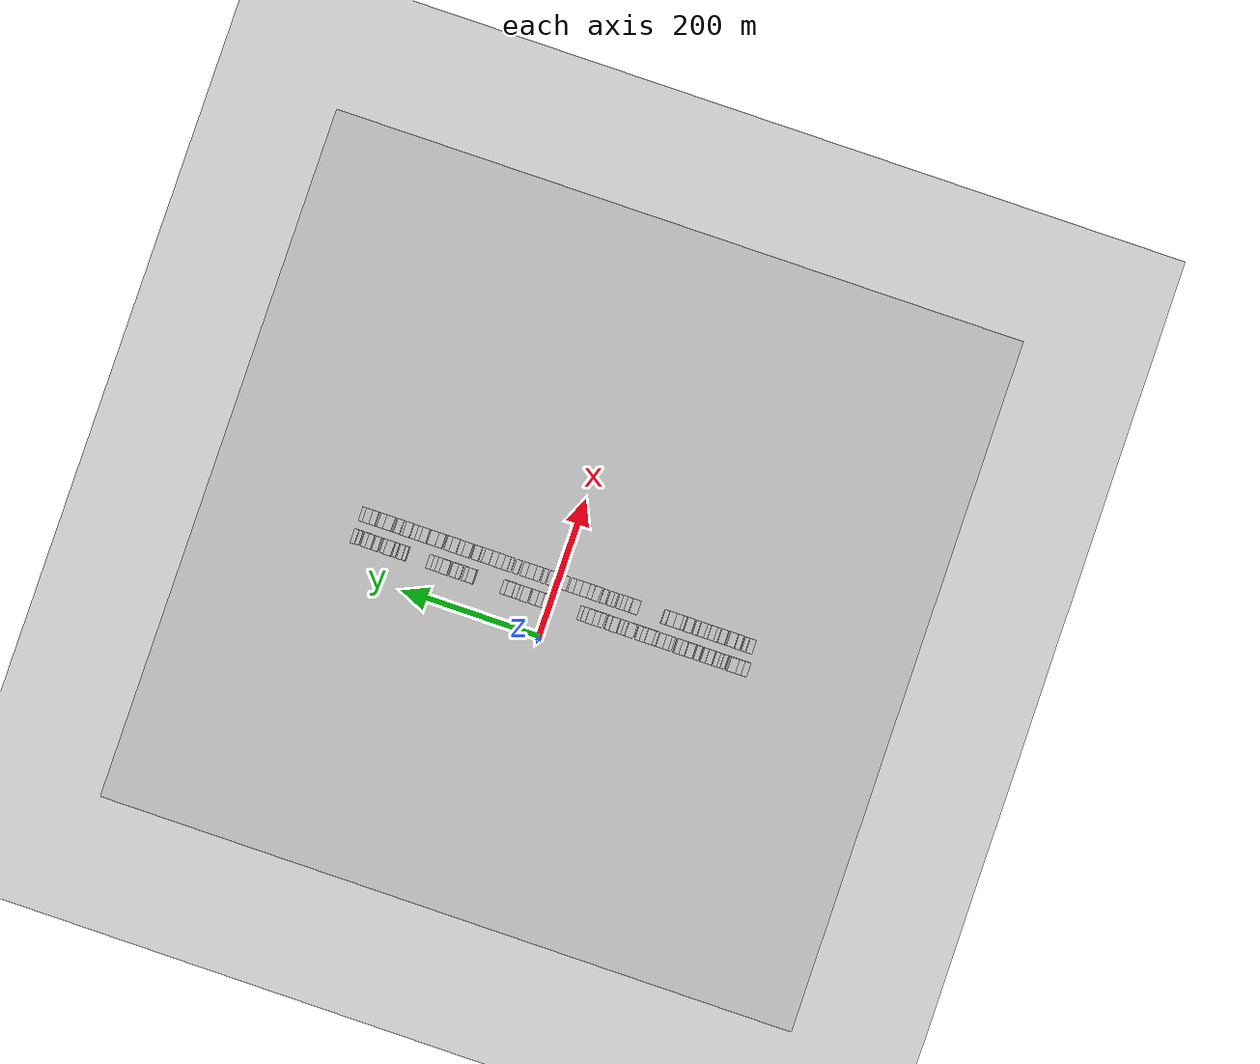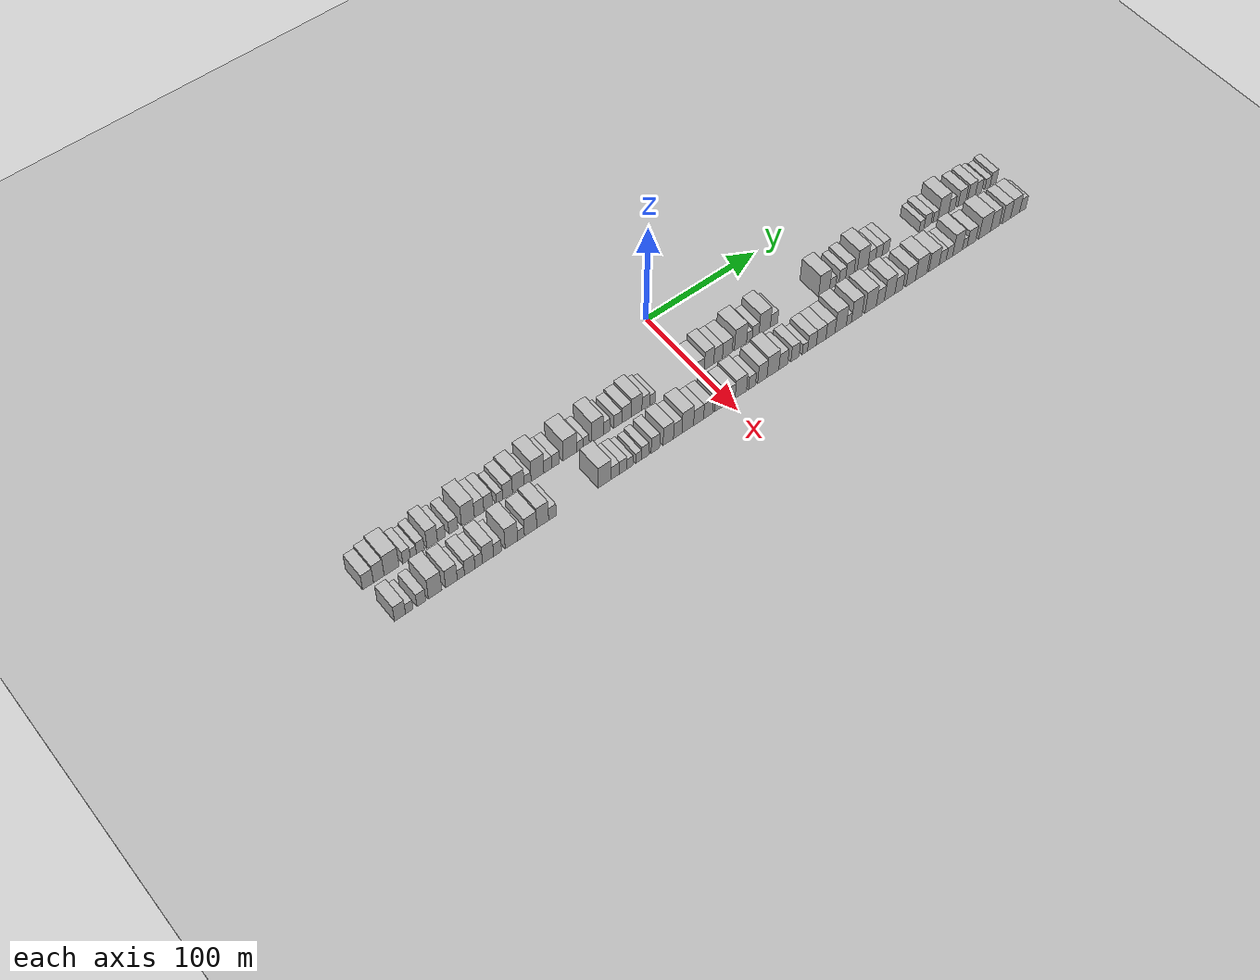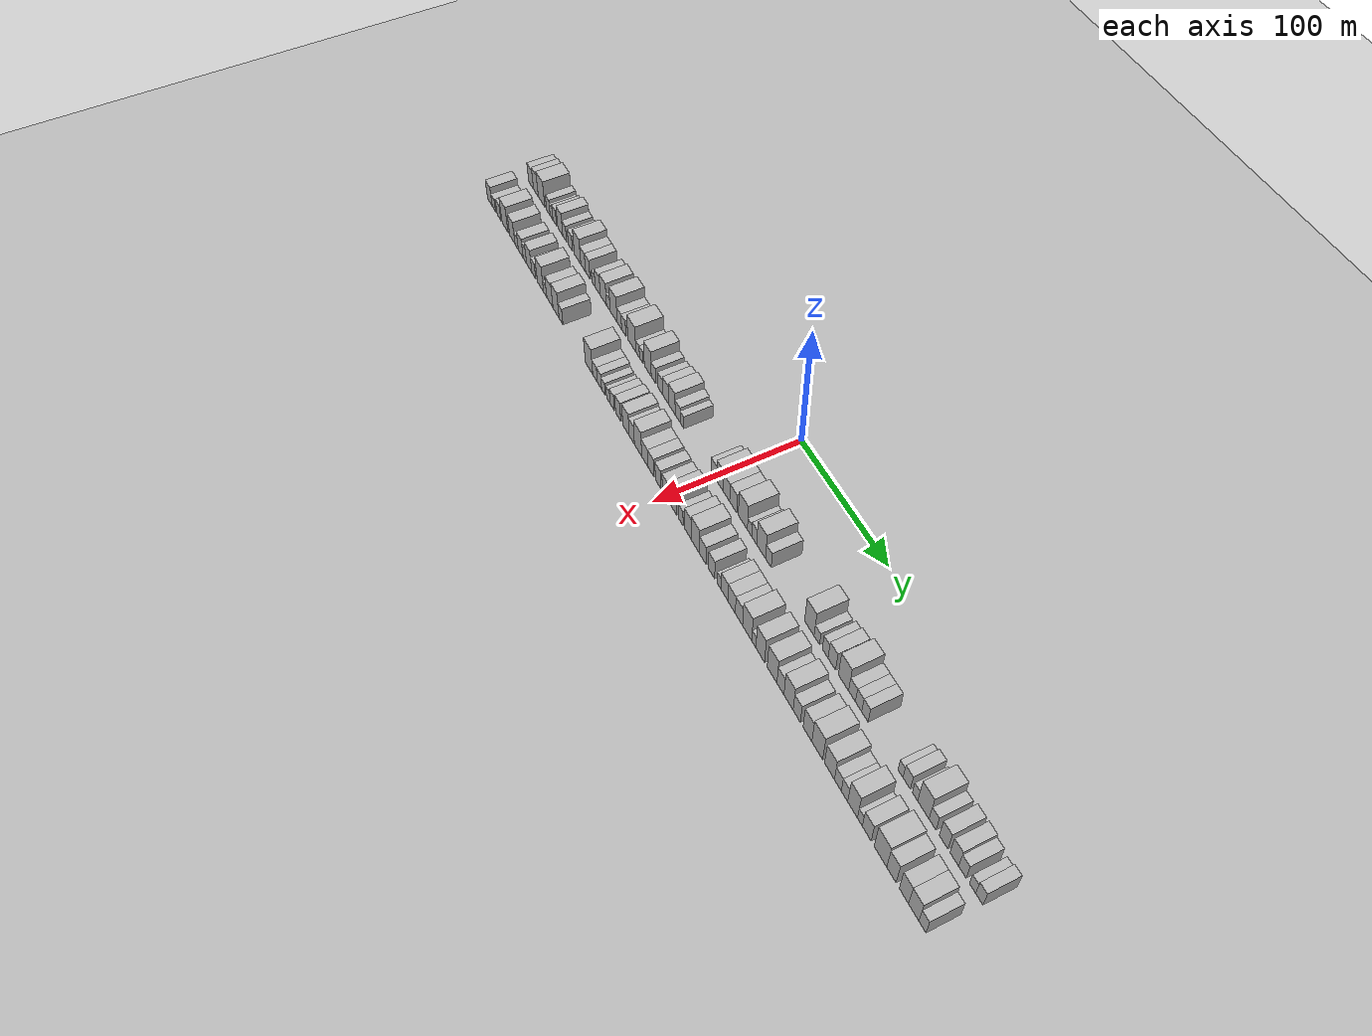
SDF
<?xml version="1.0" encoding="utf-8"?>

<sdf version="1.6">

   <world name="default">

      <gui fullscreen="0">

         <camera name="user_camera">

            <pose>-15 0 4.57585 0 0 0</pose>

            <view_controller>orbit</view_controller>

         </camera>

      </gui>

      <scene>

         <sky>

           <clouds>

             <speed>12</speed>

           </clouds>

         </sky>

         <ambient>0.4 0.4 0.4 1</ambient>

         <background>0.7 0.7 0.7 1</background>

         <shadows>1</shadows>

      </scene>

      <gravity>0 0 -9.8066</gravity>

      <magnetic_field>6e-06 2.3e-05 -4.2e-05</magnetic_field>

      <physics default="0" name="default_physics" type="ode">

         <ode>

            <solver>

               <type>quick</type>

               <iters>10</iters>

               <sor>1.0</sor>

               <use_dynamic_moi_rescaling>0</use_dynamic_moi_rescaling>

            </solver>

            <constraints>

               <cfm>0</cfm>

               <erp>0.2</erp>

               <contact_max_correcting_vel>100</contact_max_correcting_vel>

               <contact_surface_layer>0.001</contact_surface_layer>

            </constraints>

         </ode>

         <max_step_size>0.004</max_step_size>

         <real_time_factor>1</real_time_factor>

         <real_time_update_rate>250</real_time_update_rate>

      </physics>

      <light name="sun" type="directional">

         <cast_shadows>1</cast_shadows>

         <pose>0 0 10 0 0 0</pose>

         <diffuse>0.8 0.8 0.8 1</diffuse>

         <specular>0.2 0.2 0.2 1</specular>

         <attenuation>

            <range>1000</range>

            <constant>0.9</constant>

            <linear>0.01</linear>

            <quadratic>0.001</quadratic>

         </attenuation>

         <direction>-0.5 0.1 -0.9</direction>

      </light>

      <include>

         <name>ground_plane_1</name>

         <uri>model://HANNAS_ground_plane</uri>

         <pose>0 0 0  0 0 0</pose>

      </include>

      <include>

         <name>ground_plane_2</name>

         <uri>model://HANNAS_ground_plane</uri>

         <pose>100 0 0  0 0 0</pose>

      </include>

      <model name="building_1">

         <static>1</static>

         <pose frame="">50.0000 -279.7125 0 0.000000 0.000000 0.000000</pose>

         <link name="link">

            <pose frame="">0 0 9.00 0 0 0</pose>

            <collision name="collision">

               <geometry>

                  <box>

                     <size>20.0000 8.5751 18.0000</size>

                  </box>

               </geometry>

               <max_contacts>10</max_contacts>

               <surface>

                  <contact>

                     <ode/>

                  </contact>

                  <bounce/>

                  <friction>

                     <torsional>

                        <ode/>

                     </torsional>

                     <ode/>

                  </friction>

               </surface>

            </collision>

            <visual name="visual">

               <cast_shadows>0</cast_shadows>

               <geometry>

                  <box>

                     <size>20.0000 8.5751 18.0000</size>

                  </box>

               </geometry>

               <material>

                  <script>

                     <uri>model://HANNAS_wall/materials/scripts</uri>

                     <uri>model://HANNAS_wall/materials/textures</uri>

                     <name>vrc/HANNAS_wall</name>

                  </script>

               </material>

            </visual>

            <self_collide>0</self_collide>

            <enable_wind>0</enable_wind>

            <kinematic>0</kinematic>

         </link>

      </model>

      <model name="building_2">

         <static>1</static>

         <pose frame="">50.0000 -271.1900 0 0.000000 0.000000 0.000000</pose>

         <link name="link">

            <pose frame="">0 0 10.50 0 0 0</pose>

            <collision name="collision">

               <geometry>

                  <box>

                     <size>20.0000 8.4698 21.0000</size>

                  </box>

               </geometry>

               <max_contacts>10</max_contacts>

               <surface>

                  <contact>

                     <ode/>

                  </contact>

                  <bounce/>

                  <friction>

                     <torsional>

                        <ode/>

                     </torsional>

                     <ode/>

                  </friction>

               </surface>

            </collision>

            <visual name="visual">

               <cast_shadows>0</cast_shadows>

               <geometry>

                  <box>

                     <size>20.0000 8.4698 21.0000</size>

                  </box>

               </geometry>

               <material>

                  <script>

                     <uri>model://HANNAS_wall/materials/scripts</uri>

                     <uri>model://HANNAS_wall/materials/textures</uri>

                     <name>vrc/HANNAS_wall</name>

                  </script>

               </material>

            </visual>

            <self_collide>0</self_collide>

            <enable_wind>0</enable_wind>

            <kinematic>0</kinematic>

         </link>

      </model>

      <model name="building_3">

         <static>1</static>

         <pose frame="">50.0000 -261.0978 0 0.000000 0.000000 0.000000</pose>

         <link name="link">

            <pose frame="">0 0 12.00 0 0 0</pose>

            <collision name="collision">

               <geometry>

                  <box>

                     <size>20.0000 11.7146 24.0000</size>

                  </box>

               </geometry>

               <max_contacts>10</max_contacts>

               <surface>

                  <contact>

                     <ode/>

                  </contact>

                  <bounce/>

                  <friction>

                     <torsional>

                        <ode/>

                     </torsional>

                     <ode/>

                  </friction>

               </surface>

            </collision>

            <visual name="visual">

               <cast_shadows>0</cast_shadows>

               <geometry>

                  <box>

                     <size>20.0000 11.7146 24.0000</size>

                  </box>

               </geometry>

               <material>

                  <script>

                     <uri>model://HANNAS_wall/materials/scripts</uri>

                     <uri>model://HANNAS_wall/materials/textures</uri>

                     <name>vrc/HANNAS_wall</name>

                  </script>

               </material>

            </visual>

            <self_collide>0</self_collide>

            <enable_wind>0</enable_wind>

            <kinematic>0</kinematic>

         </link>

      </model>

      <model name="building_4">

         <static>1</static>

         <pose frame="">50.0000 -249.2100 0 0.000000 0.000000 0.000000</pose>

         <link name="link">

            <pose frame="">0 0 7.50 0 0 0</pose>

            <collision name="collision">

               <geometry>

                  <box>

                     <size>20.0000 6.0610 15.0000</size>

                  </box>

               </geometry>

               <max_contacts>10</max_contacts>

               <surface>

                  <contact>

                     <ode/>

                  </contact>

                  <bounce/>

                  <friction>

                     <torsional>

                        <ode/>

                     </torsional>

                     <ode/>

                  </friction>

               </surface>

            </collision>

            <visual name="visual">

               <cast_shadows>0</cast_shadows>

               <geometry>

                  <box>

                     <size>20.0000 6.0610 15.0000</size>

                  </box>

               </geometry>

               <material>

                  <script>

                     <uri>model://HANNAS_wall/materials/scripts</uri>

                     <uri>model://HANNAS_wall/materials/textures</uri>

                     <name>vrc/HANNAS_wall</name>

                  </script>

               </material>

            </visual>

            <self_collide>0</self_collide>

            <enable_wind>0</enable_wind>

            <kinematic>0</kinematic>

         </link>

      </model>

      <model name="building_5">

         <static>1</static>

         <pose frame="">50.0000 -243.7288 0 0.000000 0.000000 0.000000</pose>

         <link name="link">

            <pose frame="">0 0 6.00 0 0 0</pose>

            <collision name="collision">

               <geometry>

                  <box>

                     <size>20.0000 4.9014 12.0000</size>

                  </box>

               </geometry>

               <max_contacts>10</max_contacts>

               <surface>

                  <contact>

                     <ode/>

                  </contact>

                  <bounce/>

                  <friction>

                     <torsional>

                        <ode/>

                     </torsional>

                     <ode/>

                  </friction>

               </surface>

            </collision>

            <visual name="visual">

               <cast_shadows>0</cast_shadows>

               <geometry>

                  <box>

                     <size>20.0000 4.9014 12.0000</size>

                  </box>

               </geometry>

               <material>

                  <script>

                     <uri>model://HANNAS_wall/materials/scripts</uri>

                     <uri>model://HANNAS_wall/materials/textures</uri>

                     <name>vrc/HANNAS_wall</name>

                  </script>

               </material>

            </visual>

            <self_collide>0</self_collide>

            <enable_wind>0</enable_wind>

            <kinematic>0</kinematic>

         </link>

      </model>

      <model name="building_6">

         <static>1</static>

         <pose frame="">50.0000 -238.1100 0 0.000000 0.000000 0.000000</pose>

         <link name="link">

            <pose frame="">0 0 7.50 0 0 0</pose>

            <collision name="collision">

               <geometry>

                  <box>

                     <size>20.0000 6.3363 15.0000</size>

                  </box>

               </geometry>

               <max_contacts>10</max_contacts>

               <surface>

                  <contact>

                     <ode/>

                  </contact>

                  <bounce/>

                  <friction>

                     <torsional>

                        <ode/>

                     </torsional>

                     <ode/>

                  </friction>

               </surface>

            </collision>

            <visual name="visual">

               <cast_shadows>0</cast_shadows>

               <geometry>

                  <box>

                     <size>20.0000 6.3363 15.0000</size>

                  </box>

               </geometry>

               <material>

                  <script>

                     <uri>model://HANNAS_wall/materials/scripts</uri>

                     <uri>model://HANNAS_wall/materials/textures</uri>

                     <name>vrc/HANNAS_wall</name>

                  </script>

               </material>

            </visual>

            <self_collide>0</self_collide>

            <enable_wind>0</enable_wind>

            <kinematic>0</kinematic>

         </link>

      </model>

      <model name="building_7">

         <static>1</static>

         <pose frame="">50.0000 -228.7135 0 0.000000 0.000000 0.000000</pose>

         <link name="link">

            <pose frame="">0 0 10.50 0 0 0</pose>

            <collision name="collision">

               <geometry>

                  <box>

                     <size>20.0000 8.4566 21.0000</size>

                  </box>

               </geometry>

               <max_contacts>10</max_contacts>

               <surface>

                  <contact>

                     <ode/>

                  </contact>

                  <bounce/>

                  <friction>

                     <torsional>

                        <ode/>

                     </torsional>

                     <ode/>

                  </friction>

               </surface>

            </collision>

            <visual name="visual">

               <cast_shadows>0</cast_shadows>

               <geometry>

                  <box>

                     <size>20.0000 8.4566 21.0000</size>

                  </box>

               </geometry>

               <material>

                  <script>

                     <uri>model://HANNAS_wall/materials/scripts</uri>

                     <uri>model://HANNAS_wall/materials/textures</uri>

                     <name>vrc/HANNAS_wall</name>

                  </script>

               </material>

            </visual>

            <self_collide>0</self_collide>

            <enable_wind>0</enable_wind>

            <kinematic>0</kinematic>

         </link>

      </model>

      <model name="building_8">

         <static>1</static>

         <pose frame="">50.0000 -221.2973 0 0.000000 0.000000 0.000000</pose>

         <link name="link">

            <pose frame="">0 0 7.50 0 0 0</pose>

            <collision name="collision">

               <geometry>

                  <box>

                     <size>20.0000 6.3758 15.0000</size>

                  </box>

               </geometry>

               <max_contacts>10</max_contacts>

               <surface>

                  <contact>

                     <ode/>

                  </contact>

                  <bounce/>

                  <friction>

                     <torsional>

                        <ode/>

                     </torsional>

                     <ode/>

                  </friction>

               </surface>

            </collision>

            <visual name="visual">

               <cast_shadows>0</cast_shadows>

               <geometry>

                  <box>

                     <size>20.0000 6.3758 15.0000</size>

                  </box>

               </geometry>

               <material>

                  <script>

                     <uri>model://HANNAS_wall/materials/scripts</uri>

                     <uri>model://HANNAS_wall/materials/textures</uri>

                     <name>vrc/HANNAS_wall</name>

                  </script>

               </material>

            </visual>

            <self_collide>0</self_collide>

            <enable_wind>0</enable_wind>

            <kinematic>0</kinematic>

         </link>

      </model>

      <model name="building_9">

         <static>1</static>

         <pose frame="">50.0000 -211.5569 0 0.000000 0.000000 0.000000</pose>

         <link name="link">

            <pose frame="">0 0 7.50 0 0 0</pose>

            <collision name="collision">

               <geometry>

                  <box>

                     <size>20.0000 7.1049 15.0000</size>

                  </box>

               </geometry>

               <max_contacts>10</max_contacts>

               <surface>

                  <contact>

                     <ode/>

                  </contact>

                  <bounce/>

                  <friction>

                     <torsional>

                        <ode/>

                     </torsional>

                     <ode/>

                  </friction>

               </surface>

            </collision>

            <visual name="visual">

               <cast_shadows>0</cast_shadows>

               <geometry>

                  <box>

                     <size>20.0000 7.1049 15.0000</size>

                  </box>

               </geometry>

               <material>

                  <script>

                     <uri>model://HANNAS_wall/materials/scripts</uri>

                     <uri>model://HANNAS_wall/materials/textures</uri>

                     <name>vrc/HANNAS_wall</name>

                  </script>

               </material>

            </visual>

            <self_collide>0</self_collide>

            <enable_wind>0</enable_wind>

            <kinematic>0</kinematic>

         </link>

      </model>

      <model name="building_10">

         <static>1</static>

         <pose frame="">50.0000 -199.7303 0 0.000000 0.000000 0.000000</pose>

         <link name="link">

            <pose frame="">0 0 12.00 0 0 0</pose>

            <collision name="collision">

               <geometry>

                  <box>

                     <size>20.0000 10.5482 24.0000</size>

                  </box>

               </geometry>

               <max_contacts>10</max_contacts>

               <surface>

                  <contact>

                     <ode/>

                  </contact>

                  <bounce/>

                  <friction>

                     <torsional>

                        <ode/>

                     </torsional>

                     <ode/>

                  </friction>

               </surface>

            </collision>

            <visual name="visual">

               <cast_shadows>0</cast_shadows>

               <geometry>

                  <box>

                     <size>20.0000 10.5482 24.0000</size>

                  </box>

               </geometry>

               <material>

                  <script>

                     <uri>model://HANNAS_wall/materials/scripts</uri>

                     <uri>model://HANNAS_wall/materials/textures</uri>

                     <name>vrc/HANNAS_wall</name>

                  </script>

               </material>

            </visual>

            <self_collide>0</self_collide>

            <enable_wind>0</enable_wind>

            <kinematic>0</kinematic>

         </link>

      </model>

      <model name="building_11">

         <static>1</static>

         <pose frame="">50.0000 -190.5804 0 0.000000 0.000000 0.000000</pose>

         <link name="link">

            <pose frame="">0 0 9.00 0 0 0</pose>

            <collision name="collision">

               <geometry>

                  <box>

                     <size>20.0000 7.7517 18.0000</size>

                  </box>

               </geometry>

               <max_contacts>10</max_contacts>

               <surface>

                  <contact>

                     <ode/>

                  </contact>

                  <bounce/>

                  <friction>

                     <torsional>

                        <ode/>

                     </torsional>

                     <ode/>

                  </friction>

               </surface>

            </collision>

            <visual name="visual">

               <cast_shadows>0</cast_shadows>

               <geometry>

                  <box>

                     <size>20.0000 7.7517 18.0000</size>

                  </box>

               </geometry>

               <material>

                  <script>

                     <uri>model://HANNAS_wall/materials/scripts</uri>

                     <uri>model://HANNAS_wall/materials/textures</uri>

                     <name>vrc/HANNAS_wall</name>

                  </script>

               </material>

            </visual>

            <self_collide>0</self_collide>

            <enable_wind>0</enable_wind>

            <kinematic>0</kinematic>

         </link>

      </model>

      <model name="building_12">

         <static>1</static>

         <pose frame="">50.0000 -183.0801 0 0.000000 0.000000 0.000000</pose>

         <link name="link">

            <pose frame="">0 0 9.00 0 0 0</pose>

            <collision name="collision">

               <geometry>

                  <box>

                     <size>20.0000 7.2488 18.0000</size>

                  </box>

               </geometry>

               <max_contacts>10</max_contacts>

               <surface>

                  <contact>

                     <ode/>

                  </contact>

                  <bounce/>

                  <friction>

                     <torsional>

                        <ode/>

                     </torsional>

                     <ode/>

                  </friction>

               </surface>

            </collision>

            <visual name="visual">

               <cast_shadows>0</cast_shadows>

               <geometry>

                  <box>

                     <size>20.0000 7.2488 18.0000</size>

                  </box>

               </geometry>

               <material>

                  <script>

                     <uri>model://HANNAS_wall/materials/scripts</uri>

                     <uri>model://HANNAS_wall/materials/textures</uri>

                     <name>vrc/HANNAS_wall</name>

                  </script>

               </material>

            </visual>

            <self_collide>0</self_collide>

            <enable_wind>0</enable_wind>

            <kinematic>0</kinematic>

         </link>

      </model>

      <model name="building_13">

         <static>1</static>

         <pose frame="">50.0000 -173.7837 0 0.000000 0.000000 0.000000</pose>

         <link name="link">

            <pose frame="">0 0 6.00 0 0 0</pose>

            <collision name="collision">

               <geometry>

                  <box>

                     <size>20.0000 5.3440 12.0000</size>

                  </box>

               </geometry>

               <max_contacts>10</max_contacts>

               <surface>

                  <contact>

                     <ode/>

                  </contact>

                  <bounce/>

                  <friction>

                     <torsional>

                        <ode/>

                     </torsional>

                     <ode/>

                  </friction>

               </surface>

            </collision>

            <visual name="visual">

               <cast_shadows>0</cast_shadows>

               <geometry>

                  <box>

                     <size>20.0000 5.3440 12.0000</size>

                  </box>

               </geometry>

               <material>

                  <script>

                     <uri>model://HANNAS_wall/materials/scripts</uri>

                     <uri>model://HANNAS_wall/materials/textures</uri>

                     <name>vrc/HANNAS_wall</name>

                  </script>

               </material>

            </visual>

            <self_collide>0</self_collide>

            <enable_wind>0</enable_wind>

            <kinematic>0</kinematic>

         </link>

      </model>

      <model name="building_14">

         <static>1</static>

         <pose frame="">50.0000 -167.0755 0 0.000000 0.000000 0.000000</pose>

         <link name="link">

            <pose frame="">0 0 9.00 0 0 0</pose>

            <collision name="collision">

               <geometry>

                  <box>

                     <size>20.0000 8.0723 18.0000</size>

                  </box>

               </geometry>

               <max_contacts>10</max_contacts>

               <surface>

                  <contact>

                     <ode/>

                  </contact>

                  <bounce/>

                  <friction>

                     <torsional>

                        <ode/>

                     </torsional>

                     <ode/>

                  </friction>

               </surface>

            </collision>

            <visual name="visual">

               <cast_shadows>0</cast_shadows>

               <geometry>

                  <box>

                     <size>20.0000 8.0723 18.0000</size>

                  </box>

               </geometry>

               <material>

                  <script>

                     <uri>model://HANNAS_wall/materials/scripts</uri>

                     <uri>model://HANNAS_wall/materials/textures</uri>

                     <name>vrc/HANNAS_wall</name>

                  </script>

               </material>

            </visual>

            <self_collide>0</self_collide>

            <enable_wind>0</enable_wind>

            <kinematic>0</kinematic>

         </link>

      </model>

      <model name="building_15">

         <static>1</static>

         <pose frame="">50.0000 -158.1807 0 0.000000 0.000000 0.000000</pose>

         <link name="link">

            <pose frame="">0 0 10.50 0 0 0</pose>

            <collision name="collision">

               <geometry>

                  <box>

                     <size>20.0000 9.7175 21.0000</size>

                  </box>

               </geometry>

               <max_contacts>10</max_contacts>

               <surface>

                  <contact>

                     <ode/>

                  </contact>

                  <bounce/>

                  <friction>

                     <torsional>

                        <ode/>

                     </torsional>

                     <ode/>

                  </friction>

               </surface>

            </collision>

            <visual name="visual">

               <cast_shadows>0</cast_shadows>

               <geometry>

                  <box>

                     <size>20.0000 9.7175 21.0000</size>

                  </box>

               </geometry>

               <material>

                  <script>

                     <uri>model://HANNAS_wall/materials/scripts</uri>

                     <uri>model://HANNAS_wall/materials/textures</uri>

                     <name>vrc/HANNAS_wall</name>

                  </script>

               </material>

            </visual>

            <self_collide>0</self_collide>

            <enable_wind>0</enable_wind>

            <kinematic>0</kinematic>

         </link>

      </model>

      <model name="building_16">

         <static>1</static>

         <pose frame="">50.0000 -150.4176 0 0.000000 0.000000 0.000000</pose>

         <link name="link">

            <pose frame="">0 0 6.00 0 0 0</pose>

            <collision name="collision">

               <geometry>

                  <box>

                     <size>20.0000 5.8087 12.0000</size>

                  </box>

               </geometry>

               <max_contacts>10</max_contacts>

               <surface>

                  <contact>

                     <ode/>

                  </contact>

                  <bounce/>

                  <friction>

                     <torsional>

                        <ode/>

                     </torsional>

                     <ode/>

                  </friction>

               </surface>

            </collision>

            <visual name="visual">

               <cast_shadows>0</cast_shadows>

               <geometry>

                  <box>

                     <size>20.0000 5.8087 12.0000</size>

                  </box>

               </geometry>

               <material>

                  <script>

                     <uri>model://HANNAS_wall/materials/scripts</uri>

                     <uri>model://HANNAS_wall/materials/textures</uri>

                     <name>vrc/HANNAS_wall</name>

                  </script>

               </material>

            </visual>

            <self_collide>0</self_collide>

            <enable_wind>0</enable_wind>

            <kinematic>0</kinematic>

         </link>

      </model>

      <model name="building_17">

         <static>1</static>

         <pose frame="">50.0000 -142.1498 0 0.000000 0.000000 0.000000</pose>

         <link name="link">

            <pose frame="">0 0 12.00 0 0 0</pose>

            <collision name="collision">

               <geometry>

                  <box>

                     <size>20.0000 10.7268 24.0000</size>

                  </box>

               </geometry>

               <max_contacts>10</max_contacts>

               <surface>

                  <contact>

                     <ode/>

                  </contact>

                  <bounce/>

                  <friction>

                     <torsional>

                        <ode/>

                     </torsional>

                     <ode/>

                  </friction>

               </surface>

            </collision>

            <visual name="visual">

               <cast_shadows>0</cast_shadows>

               <geometry>

                  <box>

                     <size>20.0000 10.7268 24.0000</size>

                  </box>

               </geometry>

               <material>

                  <script>

                     <uri>model://HANNAS_wall/materials/scripts</uri>

                     <uri>model://HANNAS_wall/materials/textures</uri>

                     <name>vrc/HANNAS_wall</name>

                  </script>

               </material>

            </visual>

            <self_collide>0</self_collide>

            <enable_wind>0</enable_wind>

            <kinematic>0</kinematic>

         </link>

      </model>

      <model name="building_18">

         <static>1</static>

         <pose frame="">50.0000 -133.4117 0 0.000000 0.000000 0.000000</pose>

         <link name="link">

            <pose frame="">0 0 7.50 0 0 0</pose>

            <collision name="collision">

               <geometry>

                  <box>

                     <size>20.0000 6.7494 15.0000</size>

                  </box>

               </geometry>

               <max_contacts>10</max_contacts>

               <surface>

                  <contact>

                     <ode/>

                  </contact>

                  <bounce/>

                  <friction>

                     <torsional>

                        <ode/>

                     </torsional>

                     <ode/>

                  </friction>

               </surface>

            </collision>

            <visual name="visual">

               <cast_shadows>0</cast_shadows>

               <geometry>

                  <box>

                     <size>20.0000 6.7494 15.0000</size>

                  </box>

               </geometry>

               <material>

                  <script>

                     <uri>model://HANNAS_wall/materials/scripts</uri>

                     <uri>model://HANNAS_wall/materials/textures</uri>

                     <name>vrc/HANNAS_wall</name>

                  </script>

               </material>

            </visual>

            <self_collide>0</self_collide>

            <enable_wind>0</enable_wind>

            <kinematic>0</kinematic>

         </link>

      </model>

      <model name="building_19">

         <static>1</static>

         <pose frame="">50.0000 -126.8120 0 0.000000 0.000000 0.000000</pose>

         <link name="link">

            <pose frame="">0 0 7.50 0 0 0</pose>

            <collision name="collision">

               <geometry>

                  <box>

                     <size>20.0000 6.4500 15.0000</size>

                  </box>

               </geometry>

               <max_contacts>10</max_contacts>

               <surface>

                  <contact>

                     <ode/>

                  </contact>

                  <bounce/>

                  <friction>

                     <torsional>

                        <ode/>

                     </torsional>

                     <ode/>

                  </friction>

               </surface>

            </collision>

            <visual name="visual">

               <cast_shadows>0</cast_shadows>

               <geometry>

                  <box>

                     <size>20.0000 6.4500 15.0000</size>

                  </box>

               </geometry>

               <material>

                  <script>

                     <uri>model://HANNAS_wall/materials/scripts</uri>

                     <uri>model://HANNAS_wall/materials/textures</uri>

                     <name>vrc/HANNAS_wall</name>

                  </script>

               </material>

            </visual>

            <self_collide>0</self_collide>

            <enable_wind>0</enable_wind>

            <kinematic>0</kinematic>

         </link>

      </model>

      <model name="building_20">

         <static>1</static>

         <pose frame="">50.0000 -114.6766 0 0.000000 0.000000 0.000000</pose>

         <link name="link">

            <pose frame="">0 0 12.00 0 0 0</pose>

            <collision name="collision">

               <geometry>

                  <box>

                     <size>20.0000 11.8208 24.0000</size>

                  </box>

               </geometry>

               <max_contacts>10</max_contacts>

               <surface>

                  <contact>

                     <ode/>

                  </contact>

                  <bounce/>

                  <friction>

                     <torsional>

                        <ode/>

                     </torsional>

                     <ode/>

                  </friction>

               </surface>

            </collision>

            <visual name="visual">

               <cast_shadows>0</cast_shadows>

               <geometry>

                  <box>

                     <size>20.0000 11.8208 24.0000</size>

                  </box>

               </geometry>

               <material>

                  <script>

                     <uri>model://HANNAS_wall/materials/scripts</uri>

                     <uri>model://HANNAS_wall/materials/textures</uri>

                     <name>vrc/HANNAS_wall</name>

                  </script>

               </material>

            </visual>

            <self_collide>0</self_collide>

            <enable_wind>0</enable_wind>

            <kinematic>0</kinematic>

         </link>

      </model>

      <model name="building_21">

         <static>1</static>

         <pose frame="">50.0000 -106.0119 0 0.000000 0.000000 0.000000</pose>

         <link name="link">

            <pose frame="">0 0 6.00 0 0 0</pose>

            <collision name="collision">

               <geometry>

                  <box>

                     <size>20.0000 5.5086 12.0000</size>

                  </box>

               </geometry>

               <max_contacts>10</max_contacts>

               <surface>

                  <contact>

                     <ode/>

                  </contact>

                  <bounce/>

                  <friction>

                     <torsional>

                        <ode/>

                     </torsional>

                     <ode/>

                  </friction>

               </surface>

            </collision>

            <visual name="visual">

               <cast_shadows>0</cast_shadows>

               <geometry>

                  <box>

                     <size>20.0000 5.5086 12.0000</size>

                  </box>

               </geometry>

               <material>

                  <script>

                     <uri>model://HANNAS_wall/materials/scripts</uri>

                     <uri>model://HANNAS_wall/materials/textures</uri>

                     <name>vrc/HANNAS_wall</name>

                  </script>

               </material>

            </visual>

            <self_collide>0</self_collide>

            <enable_wind>0</enable_wind>

            <kinematic>0</kinematic>

         </link>

      </model>

      <model name="building_22">

         <static>1</static>

         <pose frame="">50.0000 -100.6855 0 0.000000 0.000000 0.000000</pose>

         <link name="link">

            <pose frame="">0 0 6.00 0 0 0</pose>

            <collision name="collision">

               <geometry>

                  <box>

                     <size>20.0000 5.1442 12.0000</size>

                  </box>

               </geometry>

               <max_contacts>10</max_contacts>

               <surface>

                  <contact>

                     <ode/>

                  </contact>

                  <bounce/>

                  <friction>

                     <torsional>

                        <ode/>

                     </torsional>

                     <ode/>

                  </friction>

               </surface>

            </collision>

            <visual name="visual">

               <cast_shadows>0</cast_shadows>

               <geometry>

                  <box>

                     <size>20.0000 5.1442 12.0000</size>

                  </box>

               </geometry>

               <material>

                  <script>

                     <uri>model://HANNAS_wall/materials/scripts</uri>

                     <uri>model://HANNAS_wall/materials/textures</uri>

                     <name>vrc/HANNAS_wall</name>

                  </script>

               </material>

            </visual>

            <self_collide>0</self_collide>

            <enable_wind>0</enable_wind>

            <kinematic>0</kinematic>

         </link>

      </model>

      <model name="building_23">

         <static>1</static>

         <pose frame="">50.0000 -91.1002 0 0.000000 0.000000 0.000000</pose>

         <link name="link">

            <pose frame="">0 0 12.00 0 0 0</pose>

            <collision name="collision">

               <geometry>

                  <box>

                     <size>20.0000 10.0264 24.0000</size>

                  </box>

               </geometry>

               <max_contacts>10</max_contacts>

               <surface>

                  <contact>

                     <ode/>

                  </contact>

                  <bounce/>

                  <friction>

                     <torsional>

                        <ode/>

                     </torsional>

                     <ode/>

                  </friction>

               </surface>

            </collision>

            <visual name="visual">

               <cast_shadows>0</cast_shadows>

               <geometry>

                  <box>

                     <size>20.0000 10.0264 24.0000</size>

                  </box>

               </geometry>

               <material>

                  <script>

                     <uri>model://HANNAS_wall/materials/scripts</uri>

                     <uri>model://HANNAS_wall/materials/textures</uri>

                     <name>vrc/HANNAS_wall</name>

                  </script>

               </material>

            </visual>

            <self_collide>0</self_collide>

            <enable_wind>0</enable_wind>

            <kinematic>0</kinematic>

         </link>

      </model>

      <model name="building_24">

         <static>1</static>

         <pose frame="">50.0000 -82.9708 0 0.000000 0.000000 0.000000</pose>

         <link name="link">

            <pose frame="">0 0 7.50 0 0 0</pose>

            <collision name="collision">

               <geometry>

                  <box>

                     <size>20.0000 6.2323 15.0000</size>

                  </box>

               </geometry>

               <max_contacts>10</max_contacts>

               <surface>

                  <contact>

                     <ode/>

                  </contact>

                  <bounce/>

                  <friction>

                     <torsional>

                        <ode/>

                     </torsional>

                     <ode/>

                  </friction>

               </surface>

            </collision>

            <visual name="visual">

               <cast_shadows>0</cast_shadows>

               <geometry>

                  <box>

                     <size>20.0000 6.2323 15.0000</size>

                  </box>

               </geometry>

               <material>

                  <script>

                     <uri>model://HANNAS_wall/materials/scripts</uri>

                     <uri>model://HANNAS_wall/materials/textures</uri>

                     <name>vrc/HANNAS_wall</name>

                  </script>

               </material>

            </visual>

            <self_collide>0</self_collide>

            <enable_wind>0</enable_wind>

            <kinematic>0</kinematic>

         </link>

      </model>

      <model name="building_25">

         <static>1</static>

         <pose frame="">50.0000 -73.3102 0 0.000000 0.000000 0.000000</pose>

         <link name="link">

            <pose frame="">0 0 7.50 0 0 0</pose>

            <collision name="collision">

               <geometry>

                  <box>

                     <size>20.0000 7.0889 15.0000</size>

                  </box>

               </geometry>

               <max_contacts>10</max_contacts>

               <surface>

                  <contact>

                     <ode/>

                  </contact>

                  <bounce/>

                  <friction>

                     <torsional>

                        <ode/>

                     </torsional>

                     <ode/>

                  </friction>

               </surface>

            </collision>

            <visual name="visual">

               <cast_shadows>0</cast_shadows>

               <geometry>

                  <box>

                     <size>20.0000 7.0889 15.0000</size>

                  </box>

               </geometry>

               <material>

                  <script>

                     <uri>model://HANNAS_wall/materials/scripts</uri>

                     <uri>model://HANNAS_wall/materials/textures</uri>

                     <name>vrc/HANNAS_wall</name>

                  </script>

               </material>

            </visual>

            <self_collide>0</self_collide>

            <enable_wind>0</enable_wind>

            <kinematic>0</kinematic>

         </link>

      </model>

      <model name="building_26">

         <static>1</static>

         <pose frame="">50.0000 -65.6326 0 0.000000 0.000000 0.000000</pose>

         <link name="link">

            <pose frame="">0 0 9.00 0 0 0</pose>

            <collision name="collision">

               <geometry>

                  <box>

                     <size>20.0000 8.2663 18.0000</size>

                  </box>

               </geometry>

               <max_contacts>10</max_contacts>

               <surface>

                  <contact>

                     <ode/>

                  </contact>

                  <bounce/>

                  <friction>

                     <torsional>

                        <ode/>

                     </torsional>

                     <ode/>

                  </friction>

               </surface>

            </collision>

            <visual name="visual">

               <cast_shadows>0</cast_shadows>

               <geometry>

                  <box>

                     <size>20.0000 8.2663 18.0000</size>

                  </box>

               </geometry>

               <material>

                  <script>

                     <uri>model://HANNAS_wall/materials/scripts</uri>

                     <uri>model://HANNAS_wall/materials/textures</uri>

                     <name>vrc/HANNAS_wall</name>

                  </script>

               </material>

            </visual>

            <self_collide>0</self_collide>

            <enable_wind>0</enable_wind>

            <kinematic>0</kinematic>

         </link>

      </model>

      <model name="building_27">

         <static>1</static>

         <pose frame="">50.0000 -56.8797 0 0.000000 0.000000 0.000000</pose>

         <link name="link">

            <pose frame="">0 0 10.50 0 0 0</pose>

            <collision name="collision">

               <geometry>

                  <box>

                     <size>20.0000 9.2396 21.0000</size>

                  </box>

               </geometry>

               <max_contacts>10</max_contacts>

               <surface>

                  <contact>

                     <ode/>

                  </contact>

                  <bounce/>

                  <friction>

                     <torsional>

                        <ode/>

                     </torsional>

                     <ode/>

                  </friction>

               </surface>

            </collision>

            <visual name="visual">

               <cast_shadows>0</cast_shadows>

               <geometry>

                  <box>

                     <size>20.0000 9.2396 21.0000</size>

                  </box>

               </geometry>

               <material>

                  <script>

                     <uri>model://HANNAS_wall/materials/scripts</uri>

                     <uri>model://HANNAS_wall/materials/textures</uri>

                     <name>vrc/HANNAS_wall</name>

                  </script>

               </material>

            </visual>

            <self_collide>0</self_collide>

            <enable_wind>0</enable_wind>

            <kinematic>0</kinematic>

         </link>

      </model>

      <model name="building_28">

         <static>1</static>

         <pose frame="">50.0000 -48.7602 0 0.000000 0.000000 0.000000</pose>

         <link name="link">

            <pose frame="">0 0 7.50 0 0 0</pose>

            <collision name="collision">

               <geometry>

                  <box>

                     <size>20.0000 6.9993 15.0000</size>

                  </box>

               </geometry>

               <max_contacts>10</max_contacts>

               <surface>

                  <contact>

                     <ode/>

                  </contact>

                  <bounce/>

                  <friction>

                     <torsional>

                        <ode/>

                     </torsional>

                     <ode/>

                  </friction>

               </surface>

            </collision>

            <visual name="visual">

               <cast_shadows>0</cast_shadows>

               <geometry>

                  <box>

                     <size>20.0000 6.9993 15.0000</size>

                  </box>

               </geometry>

               <material>

                  <script>

                     <uri>model://HANNAS_wall/materials/scripts</uri>

                     <uri>model://HANNAS_wall/materials/textures</uri>

                     <name>vrc/HANNAS_wall</name>

                  </script>

               </material>

            </visual>

            <self_collide>0</self_collide>

            <enable_wind>0</enable_wind>

            <kinematic>0</kinematic>

         </link>

      </model>

      <model name="building_29">

         <static>1</static>

         <pose frame="">50.0000 -42.7589 0 0.000000 0.000000 0.000000</pose>

         <link name="link">

            <pose frame="">0 0 6.00 0 0 0</pose>

            <collision name="collision">

               <geometry>

                  <box>

                     <size>20.0000 5.0032 12.0000</size>

                  </box>

               </geometry>

               <max_contacts>10</max_contacts>

               <surface>

                  <contact>

                     <ode/>

                  </contact>

                  <bounce/>

                  <friction>

                     <torsional>

                        <ode/>

                     </torsional>

                     <ode/>

                  </friction>

               </surface>

            </collision>

            <visual name="visual">

               <cast_shadows>0</cast_shadows>

               <geometry>

                  <box>

                     <size>20.0000 5.0032 12.0000</size>

                  </box>

               </geometry>

               <material>

                  <script>

                     <uri>model://HANNAS_wall/materials/scripts</uri>

                     <uri>model://HANNAS_wall/materials/textures</uri>

                     <name>vrc/HANNAS_wall</name>

                  </script>

               </material>

            </visual>

            <self_collide>0</self_collide>

            <enable_wind>0</enable_wind>

            <kinematic>0</kinematic>

         </link>

      </model>

      <model name="building_30">

         <static>1</static>

         <pose frame="">50.0000 -0.2794 0 0.000000 0.000000 0.000000</pose>

         <link name="link">

            <pose frame="">0 0 7.50 0 0 0</pose>

            <collision name="collision">

               <geometry>

                  <box>

                     <size>20.0000 7.3186 15.0000</size>

                  </box>

               </geometry>

               <max_contacts>10</max_contacts>

               <surface>

                  <contact>

                     <ode/>

                  </contact>

                  <bounce/>

                  <friction>

                     <torsional>

                        <ode/>

                     </torsional>

                     <ode/>

                  </friction>

               </surface>

            </collision>

            <visual name="visual">

               <cast_shadows>0</cast_shadows>

               <geometry>

                  <box>

                     <size>20.0000 7.3186 15.0000</size>

                  </box>

               </geometry>

               <material>

                  <script>

                     <uri>model://HANNAS_wall/materials/scripts</uri>

                     <uri>model://HANNAS_wall/materials/textures</uri>

                     <name>vrc/HANNAS_wall</name>

                  </script>

               </material>

            </visual>

            <self_collide>0</self_collide>

            <enable_wind>0</enable_wind>

            <kinematic>0</kinematic>

         </link>

      </model>

      <model name="building_31">

         <static>1</static>

         <pose frame="">50.0000 7.6886 0 0.000000 0.000000 0.000000</pose>

         <link name="link">

            <pose frame="">0 0 10.50 0 0 0</pose>

            <collision name="collision">

               <geometry>

                  <box>

                     <size>20.0000 8.6175 21.0000</size>

                  </box>

               </geometry>

               <max_contacts>10</max_contacts>

               <surface>

                  <contact>

                     <ode/>

                  </contact>

                  <bounce/>

                  <friction>

                     <torsional>

                        <ode/>

                     </torsional>

                     <ode/>

                  </friction>

               </surface>

            </collision>

            <visual name="visual">

               <cast_shadows>0</cast_shadows>

               <geometry>

                  <box>

                     <size>20.0000 8.6175 21.0000</size>

                  </box>

               </geometry>

               <material>

                  <script>

                     <uri>model://HANNAS_wall/materials/scripts</uri>

                     <uri>model://HANNAS_wall/materials/textures</uri>

                     <name>vrc/HANNAS_wall</name>

                  </script>

               </material>

            </visual>

            <self_collide>0</self_collide>

            <enable_wind>0</enable_wind>

            <kinematic>0</kinematic>

         </link>

      </model>

      <model name="building_32">

         <static>1</static>

         <pose frame="">50.0000 15.9778 0 0.000000 0.000000 0.000000</pose>

         <link name="link">

            <pose frame="">0 0 9.00 0 0 0</pose>

            <collision name="collision">

               <geometry>

                  <box>

                     <size>20.0000 7.9609 18.0000</size>

                  </box>

               </geometry>

               <max_contacts>10</max_contacts>

               <surface>

                  <contact>

                     <ode/>

                  </contact>

                  <bounce/>

                  <friction>

                     <torsional>

                        <ode/>

                     </torsional>

                     <ode/>

                  </friction>

               </surface>

            </collision>

            <visual name="visual">

               <cast_shadows>0</cast_shadows>

               <geometry>

                  <box>

                     <size>20.0000 7.9609 18.0000</size>

                  </box>

               </geometry>

               <material>

                  <script>

                     <uri>model://HANNAS_wall/materials/scripts</uri>

                     <uri>model://HANNAS_wall/materials/textures</uri>

                     <name>vrc/HANNAS_wall</name>

                  </script>

               </material>

            </visual>

            <self_collide>0</self_collide>

            <enable_wind>0</enable_wind>

            <kinematic>0</kinematic>

         </link>

      </model>

      <model name="building_33">

         <static>1</static>

         <pose frame="">50.0000 24.3910 0 0.000000 0.000000 0.000000</pose>

         <link name="link">

            <pose frame="">0 0 9.00 0 0 0</pose>

            <collision name="collision">

               <geometry>

                  <box>

                     <size>20.0000 8.8656 18.0000</size>

                  </box>

               </geometry>

               <max_contacts>10</max_contacts>

               <surface>

                  <contact>

                     <ode/>

                  </contact>

                  <bounce/>

                  <friction>

                     <torsional>

                        <ode/>

                     </torsional>

                     <ode/>

                  </friction>

               </surface>

            </collision>

            <visual name="visual">

               <cast_shadows>0</cast_shadows>

               <geometry>

                  <box>

                     <size>20.0000 8.8656 18.0000</size>

                  </box>

               </geometry>

               <material>

                  <script>

                     <uri>model://HANNAS_wall/materials/scripts</uri>

                     <uri>model://HANNAS_wall/materials/textures</uri>

                     <name>vrc/HANNAS_wall</name>

                  </script>

               </material>

            </visual>

            <self_collide>0</self_collide>

            <enable_wind>0</enable_wind>

            <kinematic>0</kinematic>

         </link>

      </model>

      <model name="building_34">

         <static>1</static>

         <pose frame="">50.0000 36.4261 0 0.000000 0.000000 0.000000</pose>

         <link name="link">

            <pose frame="">0 0 12.00 0 0 0</pose>

            <collision name="collision">

               <geometry>

                  <box>

                     <size>20.0000 11.2045 24.0000</size>

                  </box>

               </geometry>

               <max_contacts>10</max_contacts>

               <surface>

                  <contact>

                     <ode/>

                  </contact>

                  <bounce/>

                  <friction>

                     <torsional>

                        <ode/>

                     </torsional>

                     <ode/>

                  </friction>

               </surface>

            </collision>

            <visual name="visual">

               <cast_shadows>0</cast_shadows>

               <geometry>

                  <box>

                     <size>20.0000 11.2045 24.0000</size>

                  </box>

               </geometry>

               <material>

                  <script>

                     <uri>model://HANNAS_wall/materials/scripts</uri>

                     <uri>model://HANNAS_wall/materials/textures</uri>

                     <name>vrc/HANNAS_wall</name>

                  </script>

               </material>

            </visual>

            <self_collide>0</self_collide>

            <enable_wind>0</enable_wind>

            <kinematic>0</kinematic>

         </link>

      </model>

      <model name="building_35">

         <static>1</static>

         <pose frame="">50.0000 44.6338 0 0.000000 0.000000 0.000000</pose>

         <link name="link">

            <pose frame="">0 0 6.00 0 0 0</pose>

            <collision name="collision">

               <geometry>

                  <box>

                     <size>20.0000 5.2108 12.0000</size>

                  </box>

               </geometry>

               <max_contacts>10</max_contacts>

               <surface>

                  <contact>

                     <ode/>

                  </contact>

                  <bounce/>

                  <friction>

                     <torsional>

                        <ode/>

                     </torsional>

                     <ode/>

                  </friction>

               </surface>

            </collision>

            <visual name="visual">

               <cast_shadows>0</cast_shadows>

               <geometry>

                  <box>

                     <size>20.0000 5.2108 12.0000</size>

                  </box>

               </geometry>

               <material>

                  <script>

                     <uri>model://HANNAS_wall/materials/scripts</uri>

                     <uri>model://HANNAS_wall/materials/textures</uri>

                     <name>vrc/HANNAS_wall</name>

                  </script>

               </material>

            </visual>

            <self_collide>0</self_collide>

            <enable_wind>0</enable_wind>

            <kinematic>0</kinematic>

         </link>

      </model>

      <model name="building_36">

         <static>1</static>

         <pose frame="">50.0000 50.3678 0 0.000000 0.000000 0.000000</pose>

         <link name="link">

            <pose frame="">0 0 7.50 0 0 0</pose>

            <collision name="collision">

               <geometry>

                  <box>

                     <size>20.0000 6.2572 15.0000</size>

                  </box>

               </geometry>

               <max_contacts>10</max_contacts>

               <surface>

                  <contact>

                     <ode/>

                  </contact>

                  <bounce/>

                  <friction>

                     <torsional>

                        <ode/>

                     </torsional>

                     <ode/>

                  </friction>

               </surface>

            </collision>

            <visual name="visual">

               <cast_shadows>0</cast_shadows>

               <geometry>

                  <box>

                     <size>20.0000 6.2572 15.0000</size>

                  </box>

               </geometry>

               <material>

                  <script>

                     <uri>model://HANNAS_wall/materials/scripts</uri>

                     <uri>model://HANNAS_wall/materials/textures</uri>

                     <name>vrc/HANNAS_wall</name>

                  </script>

               </material>

            </visual>

            <self_collide>0</self_collide>

            <enable_wind>0</enable_wind>

            <kinematic>0</kinematic>

         </link>

      </model>

      <model name="building_37">

         <static>1</static>

         <pose frame="">50.0000 58.8005 0 0.000000 0.000000 0.000000</pose>

         <link name="link">

            <pose frame="">0 0 12.00 0 0 0</pose>

            <collision name="collision">

               <geometry>

                  <box>

                     <size>20.0000 10.6083 24.0000</size>

                  </box>

               </geometry>

               <max_contacts>10</max_contacts>

               <surface>

                  <contact>

                     <ode/>

                  </contact>

                  <bounce/>

                  <friction>

                     <torsional>

                        <ode/>

                     </torsional>

                     <ode/>

                  </friction>

               </surface>

            </collision>

            <visual name="visual">

               <cast_shadows>0</cast_shadows>

               <geometry>

                  <box>

                     <size>20.0000 10.6083 24.0000</size>

                  </box>

               </geometry>

               <material>

                  <script>

                     <uri>model://HANNAS_wall/materials/scripts</uri>

                     <uri>model://HANNAS_wall/materials/textures</uri>

                     <name>vrc/HANNAS_wall</name>

                  </script>

               </material>

            </visual>

            <self_collide>0</self_collide>

            <enable_wind>0</enable_wind>

            <kinematic>0</kinematic>

         </link>

      </model>

      <model name="building_38">

         <static>1</static>

         <pose frame="">50.0000 67.4824 0 0.000000 0.000000 0.000000</pose>

         <link name="link">

            <pose frame="">0 0 7.50 0 0 0</pose>

            <collision name="collision">

               <geometry>

                  <box>

                     <size>20.0000 6.7556 15.0000</size>

                  </box>

               </geometry>

               <max_contacts>10</max_contacts>

               <surface>

                  <contact>

                     <ode/>

                  </contact>

                  <bounce/>

                  <friction>

                     <torsional>

                        <ode/>

                     </torsional>

                     <ode/>

                  </friction>

               </surface>

            </collision>

            <visual name="visual">

               <cast_shadows>0</cast_shadows>

               <geometry>

                  <box>

                     <size>20.0000 6.7556 15.0000</size>

                  </box>

               </geometry>

               <material>

                  <script>

                     <uri>model://HANNAS_wall/materials/scripts</uri>

                     <uri>model://HANNAS_wall/materials/textures</uri>

                     <name>vrc/HANNAS_wall</name>

                  </script>

               </material>

            </visual>

            <self_collide>0</self_collide>

            <enable_wind>0</enable_wind>

            <kinematic>0</kinematic>

         </link>

      </model>

      <model name="building_39">

         <static>1</static>

         <pose frame="">50.0000 114.7980 0 0.000000 0.000000 0.000000</pose>

         <link name="link">

            <pose frame="">0 0 12.00 0 0 0</pose>

            <collision name="collision">

               <geometry>

                  <box>

                     <size>20.0000 10.6252 24.0000</size>

                  </box>

               </geometry>

               <max_contacts>10</max_contacts>

               <surface>

                  <contact>

                     <ode/>

                  </contact>

                  <bounce/>

                  <friction>

                     <torsional>

                        <ode/>

                     </torsional>

                     <ode/>

                  </friction>

               </surface>

            </collision>

            <visual name="visual">

               <cast_shadows>0</cast_shadows>

               <geometry>

                  <box>

                     <size>20.0000 10.6252 24.0000</size>

                  </box>

               </geometry>

               <material>

                  <script>

                     <uri>model://HANNAS_wall/materials/scripts</uri>

                     <uri>model://HANNAS_wall/materials/textures</uri>

                     <name>vrc/HANNAS_wall</name>

                  </script>

               </material>

            </visual>

            <self_collide>0</self_collide>

            <enable_wind>0</enable_wind>

            <kinematic>0</kinematic>

         </link>

      </model>

      <model name="building_40">

         <static>1</static>

         <pose frame="">50.0000 123.1017 0 0.000000 0.000000 0.000000</pose>

         <link name="link">

            <pose frame="">0 0 6.00 0 0 0</pose>

            <collision name="collision">

               <geometry>

                  <box>

                     <size>20.0000 5.9823 12.0000</size>

                  </box>

               </geometry>

               <max_contacts>10</max_contacts>

               <surface>

                  <contact>

                     <ode/>

                  </contact>

                  <bounce/>

                  <friction>

                     <torsional>

                        <ode/>

                     </torsional>

                     <ode/>

                  </friction>

               </surface>

            </collision>

            <visual name="visual">

               <cast_shadows>0</cast_shadows>

               <geometry>

                  <box>

                     <size>20.0000 5.9823 12.0000</size>

                  </box>

               </geometry>

               <material>

                  <script>

                     <uri>model://HANNAS_wall/materials/scripts</uri>

                     <uri>model://HANNAS_wall/materials/textures</uri>

                     <name>vrc/HANNAS_wall</name>

                  </script>

               </material>

            </visual>

            <self_collide>0</self_collide>

            <enable_wind>0</enable_wind>

            <kinematic>0</kinematic>

         </link>

      </model>

      <model name="building_41">

         <static>1</static>

         <pose frame="">50.0000 132.2804 0 0.000000 0.000000 0.000000</pose>

         <link name="link">

            <pose frame="">0 0 7.50 0 0 0</pose>

            <collision name="collision">

               <geometry>

                  <box>

                     <size>20.0000 6.3750 15.0000</size>

                  </box>

               </geometry>

               <max_contacts>10</max_contacts>

               <surface>

                  <contact>

                     <ode/>

                  </contact>

                  <bounce/>

                  <friction>

                     <torsional>

                        <ode/>

                     </torsional>

                     <ode/>

                  </friction>

               </surface>

            </collision>

            <visual name="visual">

               <cast_shadows>0</cast_shadows>

               <geometry>

                  <box>

                     <size>20.0000 6.3750 15.0000</size>

                  </box>

               </geometry>

               <material>

                  <script>

                     <uri>model://HANNAS_wall/materials/scripts</uri>

                     <uri>model://HANNAS_wall/materials/textures</uri>

                     <name>vrc/HANNAS_wall</name>

                  </script>

               </material>

            </visual>

            <self_collide>0</self_collide>

            <enable_wind>0</enable_wind>

            <kinematic>0</kinematic>

         </link>

      </model>

      <model name="building_42">

         <static>1</static>

         <pose frame="">50.0000 139.5028 0 0.000000 0.000000 0.000000</pose>

         <link name="link">

            <pose frame="">0 0 9.00 0 0 0</pose>

            <collision name="collision">

               <geometry>

                  <box>

                     <size>20.0000 8.0697 18.0000</size>

                  </box>

               </geometry>

               <max_contacts>10</max_contacts>

               <surface>

                  <contact>

                     <ode/>

                  </contact>

                  <bounce/>

                  <friction>

                     <torsional>

                        <ode/>

                     </torsional>

                     <ode/>

                  </friction>

               </surface>

            </collision>

            <visual name="visual">

               <cast_shadows>0</cast_shadows>

               <geometry>

                  <box>

                     <size>20.0000 8.0697 18.0000</size>

                  </box>

               </geometry>

               <material>

                  <script>

                     <uri>model://HANNAS_wall/materials/scripts</uri>

                     <uri>model://HANNAS_wall/materials/textures</uri>

                     <name>vrc/HANNAS_wall</name>

                  </script>

               </material>

            </visual>

            <self_collide>0</self_collide>

            <enable_wind>0</enable_wind>

            <kinematic>0</kinematic>

         </link>

      </model>

      <model name="building_43">

         <static>1</static>

         <pose frame="">50.0000 151.9790 0 0.000000 0.000000 0.000000</pose>

         <link name="link">

            <pose frame="">0 0 12.00 0 0 0</pose>

            <collision name="collision">

               <geometry>

                  <box>

                     <size>20.0000 10.8826 24.0000</size>

                  </box>

               </geometry>

               <max_contacts>10</max_contacts>

               <surface>

                  <contact>

                     <ode/>

                  </contact>

                  <bounce/>

                  <friction>

                     <torsional>

                        <ode/>

                     </torsional>

                     <ode/>

                  </friction>

               </surface>

            </collision>

            <visual name="visual">

               <cast_shadows>0</cast_shadows>

               <geometry>

                  <box>

                     <size>20.0000 10.8826 24.0000</size>

                  </box>

               </geometry>

               <material>

                  <script>

                     <uri>model://HANNAS_wall/materials/scripts</uri>

                     <uri>model://HANNAS_wall/materials/textures</uri>

                     <name>vrc/HANNAS_wall</name>

                  </script>

               </material>

            </visual>

            <self_collide>0</self_collide>

            <enable_wind>0</enable_wind>

            <kinematic>0</kinematic>

         </link>

      </model>

      <model name="building_44">

         <static>1</static>

         <pose frame="">50.0000 161.0031 0 0.000000 0.000000 0.000000</pose>

         <link name="link">

            <pose frame="">0 0 7.50 0 0 0</pose>

            <collision name="collision">

               <geometry>

                  <box>

                     <size>20.0000 7.1656 15.0000</size>

                  </box>

               </geometry>

               <max_contacts>10</max_contacts>

               <surface>

                  <contact>

                     <ode/>

                  </contact>

                  <bounce/>

                  <friction>

                     <torsional>

                        <ode/>

                     </torsional>

                     <ode/>

                  </friction>

               </surface>

            </collision>

            <visual name="visual">

               <cast_shadows>0</cast_shadows>

               <geometry>

                  <box>

                     <size>20.0000 7.1656 15.0000</size>

                  </box>

               </geometry>

               <material>

                  <script>

                     <uri>model://HANNAS_wall/materials/scripts</uri>

                     <uri>model://HANNAS_wall/materials/textures</uri>

                     <name>vrc/HANNAS_wall</name>

                  </script>

               </material>

            </visual>

            <self_collide>0</self_collide>

            <enable_wind>0</enable_wind>

            <kinematic>0</kinematic>

         </link>

      </model>

      <model name="building_45">

         <static>1</static>

         <pose frame="">50.0000 167.8345 0 0.000000 0.000000 0.000000</pose>

         <link name="link">

            <pose frame="">0 0 7.50 0 0 0</pose>

            <collision name="collision">

               <geometry>

                  <box>

                     <size>20.0000 6.4972 15.0000</size>

                  </box>

               </geometry>

               <max_contacts>10</max_contacts>

               <surface>

                  <contact>

                     <ode/>

                  </contact>

                  <bounce/>

                  <friction>

                     <torsional>

                        <ode/>

                     </torsional>

                     <ode/>

                  </friction>

               </surface>

            </collision>

            <visual name="visual">

               <cast_shadows>0</cast_shadows>

               <geometry>

                  <box>

                     <size>20.0000 6.4972 15.0000</size>

                  </box>

               </geometry>

               <material>

                  <script>

                     <uri>model://HANNAS_wall/materials/scripts</uri>

                     <uri>model://HANNAS_wall/materials/textures</uri>

                     <name>vrc/HANNAS_wall</name>

                  </script>

               </material>

            </visual>

            <self_collide>0</self_collide>

            <enable_wind>0</enable_wind>

            <kinematic>0</kinematic>

         </link>

      </model>

      <model name="building_46">

         <static>1</static>

         <pose frame="">50.0000 174.4010 0 0.000000 0.000000 0.000000</pose>

         <link name="link">

            <pose frame="">0 0 7.50 0 0 0</pose>

            <collision name="collision">

               <geometry>

                  <box>

                     <size>20.0000 6.6358 15.0000</size>

                  </box>

               </geometry>

               <max_contacts>10</max_contacts>

               <surface>

                  <contact>

                     <ode/>

                  </contact>

                  <bounce/>

                  <friction>

                     <torsional>

                        <ode/>

                     </torsional>

                     <ode/>

                  </friction>

               </surface>

            </collision>

            <visual name="visual">

               <cast_shadows>0</cast_shadows>

               <geometry>

                  <box>

                     <size>20.0000 6.6358 15.0000</size>

                  </box>

               </geometry>

               <material>

                  <script>

                     <uri>model://HANNAS_wall/materials/scripts</uri>

                     <uri>model://HANNAS_wall/materials/textures</uri>

                     <name>vrc/HANNAS_wall</name>

                  </script>

               </material>

            </visual>

            <self_collide>0</self_collide>

            <enable_wind>0</enable_wind>

            <kinematic>0</kinematic>

         </link>

      </model>

      <model name="building_47">

         <static>1</static>

         <pose frame="">50.0000 210.0900 0 0.000000 0.000000 0.000000</pose>

         <link name="link">

            <pose frame="">0 0 6.00 0 0 0</pose>

            <collision name="collision">

               <geometry>

                  <box>

                     <size>20.0000 4.9141 12.0000</size>

                  </box>

               </geometry>

               <max_contacts>10</max_contacts>

               <surface>

                  <contact>

                     <ode/>

                  </contact>

                  <bounce/>

                  <friction>

                     <torsional>

                        <ode/>

                     </torsional>

                     <ode/>

                  </friction>

               </surface>

            </collision>

            <visual name="visual">

               <cast_shadows>0</cast_shadows>

               <geometry>

                  <box>

                     <size>20.0000 4.9141 12.0000</size>

                  </box>

               </geometry>

               <material>

                  <script>

                     <uri>model://HANNAS_wall/materials/scripts</uri>

                     <uri>model://HANNAS_wall/materials/textures</uri>

                     <name>vrc/HANNAS_wall</name>

                  </script>

               </material>

            </visual>

            <self_collide>0</self_collide>

            <enable_wind>0</enable_wind>

            <kinematic>0</kinematic>

         </link>

      </model>

      <model name="building_48">

         <static>1</static>

         <pose frame="">50.0000 216.0819 0 0.000000 0.000000 0.000000</pose>

         <link name="link">

            <pose frame="">0 0 7.50 0 0 0</pose>

            <collision name="collision">

               <geometry>

                  <box>

                     <size>20.0000 7.0696 15.0000</size>

                  </box>

               </geometry>

               <max_contacts>10</max_contacts>

               <surface>

                  <contact>

                     <ode/>

                  </contact>

                  <bounce/>

                  <friction>

                     <torsional>

                        <ode/>

                     </torsional>

                     <ode/>

                  </friction>

               </surface>

            </collision>

            <visual name="visual">

               <cast_shadows>0</cast_shadows>

               <geometry>

                  <box>

                     <size>20.0000 7.0696 15.0000</size>

                  </box>

               </geometry>

               <material>

                  <script>

                     <uri>model://HANNAS_wall/materials/scripts</uri>

                     <uri>model://HANNAS_wall/materials/textures</uri>

                     <name>vrc/HANNAS_wall</name>

                  </script>

               </material>

            </visual>

            <self_collide>0</self_collide>

            <enable_wind>0</enable_wind>

            <kinematic>0</kinematic>

         </link>

      </model>

      <model name="building_49">

         <static>1</static>

         <pose frame="">50.0000 224.1275 0 0.000000 0.000000 0.000000</pose>

         <link name="link">

            <pose frame="">0 0 6.00 0 0 0</pose>

            <collision name="collision">

               <geometry>

                  <box>

                     <size>20.0000 5.0218 12.0000</size>

                  </box>

               </geometry>

               <max_contacts>10</max_contacts>

               <surface>

                  <contact>

                     <ode/>

                  </contact>

                  <bounce/>

                  <friction>

                     <torsional>

                        <ode/>

                     </torsional>

                     <ode/>

                  </friction>

               </surface>

            </collision>

            <visual name="visual">

               <cast_shadows>0</cast_shadows>

               <geometry>

                  <box>

                     <size>20.0000 5.0218 12.0000</size>

                  </box>

               </geometry>

               <material>

                  <script>

                     <uri>model://HANNAS_wall/materials/scripts</uri>

                     <uri>model://HANNAS_wall/materials/textures</uri>

                     <name>vrc/HANNAS_wall</name>

                  </script>

               </material>

            </visual>

            <self_collide>0</self_collide>

            <enable_wind>0</enable_wind>

            <kinematic>0</kinematic>

         </link>

      </model>

      <model name="building_50">

         <static>1</static>

         <pose frame="">50.0000 232.0344 0 0.000000 0.000000 0.000000</pose>

         <link name="link">

            <pose frame="">0 0 12.00 0 0 0</pose>

            <collision name="collision">

               <geometry>

                  <box>

                     <size>20.0000 10.7920 24.0000</size>

                  </box>

               </geometry>

               <max_contacts>10</max_contacts>

               <surface>

                  <contact>

                     <ode/>

                  </contact>

                  <bounce/>

                  <friction>

                     <torsional>

                        <ode/>

                     </torsional>

                     <ode/>

                  </friction>

               </surface>

            </collision>

            <visual name="visual">

               <cast_shadows>0</cast_shadows>

               <geometry>

                  <box>

                     <size>20.0000 10.7920 24.0000</size>

                  </box>

               </geometry>

               <material>

                  <script>

                     <uri>model://HANNAS_wall/materials/scripts</uri>

                     <uri>model://HANNAS_wall/materials/textures</uri>

                     <name>vrc/HANNAS_wall</name>

                  </script>

               </material>

            </visual>

            <self_collide>0</self_collide>

            <enable_wind>0</enable_wind>

            <kinematic>0</kinematic>

         </link>

      </model>

      <model name="building_51">

         <static>1</static>

         <pose frame="">50.0000 240.6646 0 0.000000 0.000000 0.000000</pose>

         <link name="link">

            <pose frame="">0 0 7.50 0 0 0</pose>

            <collision name="collision">

               <geometry>

                  <box>

                     <size>20.0000 6.4684 15.0000</size>

                  </box>

               </geometry>

               <max_contacts>10</max_contacts>

               <surface>

                  <contact>

                     <ode/>

                  </contact>

                  <bounce/>

                  <friction>

                     <torsional>

                        <ode/>

                     </torsional>

                     <ode/>

                  </friction>

               </surface>

            </collision>

            <visual name="visual">

               <cast_shadows>0</cast_shadows>

               <geometry>

                  <box>

                     <size>20.0000 6.4684 15.0000</size>

                  </box>

               </geometry>

               <material>

                  <script>

                     <uri>model://HANNAS_wall/materials/scripts</uri>

                     <uri>model://HANNAS_wall/materials/textures</uri>

                     <name>vrc/HANNAS_wall</name>

                  </script>

               </material>

            </visual>

            <self_collide>0</self_collide>

            <enable_wind>0</enable_wind>

            <kinematic>0</kinematic>

         </link>

      </model>

      <model name="building_52">

         <static>1</static>

         <pose frame="">50.0000 250.8795 0 0.000000 0.000000 0.000000</pose>

         <link name="link">

            <pose frame="">0 0 9.00 0 0 0</pose>

            <collision name="collision">

               <geometry>

                  <box>

                     <size>20.0000 7.9615 18.0000</size>

                  </box>

               </geometry>

               <max_contacts>10</max_contacts>

               <surface>

                  <contact>

                     <ode/>

                  </contact>

                  <bounce/>

                  <friction>

                     <torsional>

                        <ode/>

                     </torsional>

                     <ode/>

                  </friction>

               </surface>

            </collision>

            <visual name="visual">

               <cast_shadows>0</cast_shadows>

               <geometry>

                  <box>

                     <size>20.0000 7.9615 18.0000</size>

                  </box>

               </geometry>

               <material>

                  <script>

                     <uri>model://HANNAS_wall/materials/scripts</uri>

                     <uri>model://HANNAS_wall/materials/textures</uri>

                     <name>vrc/HANNAS_wall</name>

                  </script>

               </material>

            </visual>

            <self_collide>0</self_collide>

            <enable_wind>0</enable_wind>

            <kinematic>0</kinematic>

         </link>

      </model>

      <model name="building_53">

         <static>1</static>

         <pose frame="">50.0000 260.7514 0 0.000000 0.000000 0.000000</pose>

         <link name="link">

            <pose frame="">0 0 9.00 0 0 0</pose>

            <collision name="collision">

               <geometry>

                  <box>

                     <size>20.0000 7.7824 18.0000</size>

                  </box>

               </geometry>

               <max_contacts>10</max_contacts>

               <surface>

                  <contact>

                     <ode/>

                  </contact>

                  <bounce/>

                  <friction>

                     <torsional>

                        <ode/>

                     </torsional>

                     <ode/>

                  </friction>

               </surface>

            </collision>

            <visual name="visual">

               <cast_shadows>0</cast_shadows>

               <geometry>

                  <box>

                     <size>20.0000 7.7824 18.0000</size>

                  </box>

               </geometry>

               <material>

                  <script>

                     <uri>model://HANNAS_wall/materials/scripts</uri>

                     <uri>model://HANNAS_wall/materials/textures</uri>

                     <name>vrc/HANNAS_wall</name>

                  </script>

               </material>

            </visual>

            <self_collide>0</self_collide>

            <enable_wind>0</enable_wind>

            <kinematic>0</kinematic>

         </link>

      </model>

      <model name="building_54">

         <static>1</static>

         <pose frame="">50.0000 267.9946 0 0.000000 0.000000 0.000000</pose>

         <link name="link">

            <pose frame="">0 0 7.50 0 0 0</pose>

            <collision name="collision">

               <geometry>

                  <box>

                     <size>20.0000 6.7040 15.0000</size>

                  </box>

               </geometry>

               <max_contacts>10</max_contacts>

               <surface>

                  <contact>

                     <ode/>

                  </contact>

                  <bounce/>

                  <friction>

                     <torsional>

                        <ode/>

                     </torsional>

                     <ode/>

                  </friction>

               </surface>

            </collision>

            <visual name="visual">

               <cast_shadows>0</cast_shadows>

               <geometry>

                  <box>

                     <size>20.0000 6.7040 15.0000</size>

                  </box>

               </geometry>

               <material>

                  <script>

                     <uri>model://HANNAS_wall/materials/scripts</uri>

                     <uri>model://HANNAS_wall/materials/textures</uri>

                     <name>vrc/HANNAS_wall</name>

                  </script>

               </material>

            </visual>

            <self_collide>0</self_collide>

            <enable_wind>0</enable_wind>

            <kinematic>0</kinematic>

         </link>

      </model>

      <model name="building_55">

         <static>1</static>

         <pose frame="">50.0000 277.1277 0 0.000000 0.000000 0.000000</pose>

         <link name="link">

            <pose frame="">0 0 6.00 0 0 0</pose>

            <collision name="collision">

               <geometry>

                  <box>

                     <size>20.0000 5.5620 12.0000</size>

                  </box>

               </geometry>

               <max_contacts>10</max_contacts>

               <surface>

                  <contact>

                     <ode/>

                  </contact>

                  <bounce/>

                  <friction>

                     <torsional>

                        <ode/>

                     </torsional>

                     <ode/>

                  </friction>

               </surface>

            </collision>

            <visual name="visual">

               <cast_shadows>0</cast_shadows>

               <geometry>

                  <box>

                     <size>20.0000 5.5620 12.0000</size>

                  </box>

               </geometry>

               <material>

                  <script>

                     <uri>model://HANNAS_wall/materials/scripts</uri>

                     <uri>model://HANNAS_wall/materials/textures</uri>

                     <name>vrc/HANNAS_wall</name>

                  </script>

               </material>

            </visual>

            <self_collide>0</self_collide>

            <enable_wind>0</enable_wind>

            <kinematic>0</kinematic>

         </link>

      </model>

      <model name="building_56">

         <static>1</static>

         <pose frame="">50.0000 283.1235 0 0.000000 0.000000 0.000000</pose>

         <link name="link">

            <pose frame="">0 0 7.50 0 0 0</pose>

            <collision name="collision">

               <geometry>

                  <box>

                     <size>20.0000 6.4297 15.0000</size>

                  </box>

               </geometry>

               <max_contacts>10</max_contacts>

               <surface>

                  <contact>

                     <ode/>

                  </contact>

                  <bounce/>

                  <friction>

                     <torsional>

                        <ode/>

                     </torsional>

                     <ode/>

                  </friction>

               </surface>

            </collision>

            <visual name="visual">

               <cast_shadows>0</cast_shadows>

               <geometry>

                  <box>

                     <size>20.0000 6.4297 15.0000</size>

                  </box>

               </geometry>

               <material>

                  <script>

                     <uri>model://HANNAS_wall/materials/scripts</uri>

                     <uri>model://HANNAS_wall/materials/textures</uri>

                     <name>vrc/HANNAS_wall</name>

                  </script>

               </material>

            </visual>

            <self_collide>0</self_collide>

            <enable_wind>0</enable_wind>

            <kinematic>0</kinematic>

         </link>

      </model>

      <model name="building_57">

         <static>1</static>

         <pose frame="">82.0000 -276.6978 0 0.000000 0.000000 0.000000</pose>

         <link name="link">

            <pose frame="">0 0 9.00 0 0 0</pose>

            <collision name="collision">

               <geometry>

                  <box>

                     <size>20.0000 8.6043 18.0000</size>

                  </box>

               </geometry>

               <max_contacts>10</max_contacts>

               <surface>

                  <contact>

                     <ode/>

                  </contact>

                  <bounce/>

                  <friction>

                     <torsional>

                        <ode/>

                     </torsional>

                     <ode/>

                  </friction>

               </surface>

            </collision>

            <visual name="visual">

               <cast_shadows>0</cast_shadows>

               <geometry>

                  <box>

                     <size>20.0000 8.6043 18.0000</size>

                  </box>

               </geometry>

               <material>

                  <script>

                     <uri>model://HANNAS_wall/materials/scripts</uri>

                     <uri>model://HANNAS_wall/materials/textures</uri>

                     <name>vrc/HANNAS_wall</name>

                  </script>

               </material>

            </visual>

            <self_collide>0</self_collide>

            <enable_wind>0</enable_wind>

            <kinematic>0</kinematic>

         </link>

      </model>

      <model name="building_58">

         <static>1</static>

         <pose frame="">82.0000 -269.4161 0 0.000000 0.000000 0.000000</pose>

         <link name="link">

            <pose frame="">0 0 6.00 0 0 0</pose>

            <collision name="collision">

               <geometry>

                  <box>

                     <size>20.0000 5.9592 12.0000</size>

                  </box>

               </geometry>

               <max_contacts>10</max_contacts>

               <surface>

                  <contact>

                     <ode/>

                  </contact>

                  <bounce/>

                  <friction>

                     <torsional>

                        <ode/>

                     </torsional>

                     <ode/>

                  </friction>

               </surface>

            </collision>

            <visual name="visual">

               <cast_shadows>0</cast_shadows>

               <geometry>

                  <box>

                     <size>20.0000 5.9592 12.0000</size>

                  </box>

               </geometry>

               <material>

                  <script>

                     <uri>model://HANNAS_wall/materials/scripts</uri>

                     <uri>model://HANNAS_wall/materials/textures</uri>

                     <name>vrc/HANNAS_wall</name>

                  </script>

               </material>

            </visual>

            <self_collide>0</self_collide>

            <enable_wind>0</enable_wind>

            <kinematic>0</kinematic>

         </link>

      </model>

      <model name="building_59">

         <static>1</static>

         <pose frame="">82.0000 -259.9107 0 0.000000 0.000000 0.000000</pose>

         <link name="link">

            <pose frame="">0 0 7.50 0 0 0</pose>

            <collision name="collision">

               <geometry>

                  <box>

                     <size>20.0000 7.0517 15.0000</size>

                  </box>

               </geometry>

               <max_contacts>10</max_contacts>

               <surface>

                  <contact>

                     <ode/>

                  </contact>

                  <bounce/>

                  <friction>

                     <torsional>

                        <ode/>

                     </torsional>

                     <ode/>

                  </friction>

               </surface>

            </collision>

            <visual name="visual">

               <cast_shadows>0</cast_shadows>

               <geometry>

                  <box>

                     <size>20.0000 7.0517 15.0000</size>

                  </box>

               </geometry>

               <material>

                  <script>

                     <uri>model://HANNAS_wall/materials/scripts</uri>

                     <uri>model://HANNAS_wall/materials/textures</uri>

                     <name>vrc/HANNAS_wall</name>

                  </script>

               </material>

            </visual>

            <self_collide>0</self_collide>

            <enable_wind>0</enable_wind>

            <kinematic>0</kinematic>

         </link>

      </model>

      <model name="building_60">

         <static>1</static>

         <pose frame="">82.0000 -249.0382 0 0.000000 0.000000 0.000000</pose>

         <link name="link">

            <pose frame="">0 0 12.00 0 0 0</pose>

            <collision name="collision">

               <geometry>

                  <box>

                     <size>20.0000 10.6934 24.0000</size>

                  </box>

               </geometry>

               <max_contacts>10</max_contacts>

               <surface>

                  <contact>

                     <ode/>

                  </contact>

                  <bounce/>

                  <friction>

                     <torsional>

                        <ode/>

                     </torsional>

                     <ode/>

                  </friction>

               </surface>

            </collision>

            <visual name="visual">

               <cast_shadows>0</cast_shadows>

               <geometry>

                  <box>

                     <size>20.0000 10.6934 24.0000</size>

                  </box>

               </geometry>

               <material>

                  <script>

                     <uri>model://HANNAS_wall/materials/scripts</uri>

                     <uri>model://HANNAS_wall/materials/textures</uri>

                     <name>vrc/HANNAS_wall</name>

                  </script>

               </material>

            </visual>

            <self_collide>0</self_collide>

            <enable_wind>0</enable_wind>

            <kinematic>0</kinematic>

         </link>

      </model>

      <model name="building_61">

         <static>1</static>

         <pose frame="">82.0000 -236.0178 0 0.000000 0.000000 0.000000</pose>

         <link name="link">

            <pose frame="">0 0 10.50 0 0 0</pose>

            <collision name="collision">

               <geometry>

                  <box>

                     <size>20.0000 9.3474 21.0000</size>

                  </box>

               </geometry>

               <max_contacts>10</max_contacts>

               <surface>

                  <contact>

                     <ode/>

                  </contact>

                  <bounce/>

                  <friction>

                     <torsional>

                        <ode/>

                     </torsional>

                     <ode/>

                  </friction>

               </surface>

            </collision>

            <visual name="visual">

               <cast_shadows>0</cast_shadows>

               <geometry>

                  <box>

                     <size>20.0000 9.3474 21.0000</size>

                  </box>

               </geometry>

               <material>

                  <script>

                     <uri>model://HANNAS_wall/materials/scripts</uri>

                     <uri>model://HANNAS_wall/materials/textures</uri>

                     <name>vrc/HANNAS_wall</name>

                  </script>

               </material>

            </visual>

            <self_collide>0</self_collide>

            <enable_wind>0</enable_wind>

            <kinematic>0</kinematic>

         </link>

      </model>

      <model name="building_62">

         <static>1</static>

         <pose frame="">82.0000 -228.4459 0 0.000000 0.000000 0.000000</pose>

         <link name="link">

            <pose frame="">0 0 6.00 0 0 0</pose>

            <collision name="collision">

               <geometry>

                  <box>

                     <size>20.0000 5.7963 12.0000</size>

                  </box>

               </geometry>

               <max_contacts>10</max_contacts>

               <surface>

                  <contact>

                     <ode/>

                  </contact>

                  <bounce/>

                  <friction>

                     <torsional>

                        <ode/>

                     </torsional>

                     <ode/>

                  </friction>

               </surface>

            </collision>

            <visual name="visual">

               <cast_shadows>0</cast_shadows>

               <geometry>

                  <box>

                     <size>20.0000 5.7963 12.0000</size>

                  </box>

               </geometry>

               <material>

                  <script>

                     <uri>model://HANNAS_wall/materials/scripts</uri>

                     <uri>model://HANNAS_wall/materials/textures</uri>

                     <name>vrc/HANNAS_wall</name>

                  </script>

               </material>

            </visual>

            <self_collide>0</self_collide>

            <enable_wind>0</enable_wind>

            <kinematic>0</kinematic>

         </link>

      </model>

      <model name="building_63">

         <static>1</static>

         <pose frame="">82.0000 -221.3331 0 0.000000 0.000000 0.000000</pose>

         <link name="link">

            <pose frame="">0 0 9.00 0 0 0</pose>

            <collision name="collision">

               <geometry>

                  <box>

                     <size>20.0000 8.4293 18.0000</size>

                  </box>

               </geometry>

               <max_contacts>10</max_contacts>

               <surface>

                  <contact>

                     <ode/>

                  </contact>

                  <bounce/>

                  <friction>

                     <torsional>

                        <ode/>

                     </torsional>

                     <ode/>

                  </friction>

               </surface>

            </collision>

            <visual name="visual">

               <cast_shadows>0</cast_shadows>

               <geometry>

                  <box>

                     <size>20.0000 8.4293 18.0000</size>

                  </box>

               </geometry>

               <material>

                  <script>

                     <uri>model://HANNAS_wall/materials/scripts</uri>

                     <uri>model://HANNAS_wall/materials/textures</uri>

                     <name>vrc/HANNAS_wall</name>

                  </script>

               </material>

            </visual>

            <self_collide>0</self_collide>

            <enable_wind>0</enable_wind>

            <kinematic>0</kinematic>

         </link>

      </model>

      <model name="building_64">

         <static>1</static>

         <pose frame="">82.0000 -214.1167 0 0.000000 0.000000 0.000000</pose>

         <link name="link">

            <pose frame="">0 0 7.50 0 0 0</pose>

            <collision name="collision">

               <geometry>

                  <box>

                     <size>20.0000 6.0035 15.0000</size>

                  </box>

               </geometry>

               <max_contacts>10</max_contacts>

               <surface>

                  <contact>

                     <ode/>

                  </contact>

                  <bounce/>

                  <friction>

                     <torsional>

                        <ode/>

                     </torsional>

                     <ode/>

                  </friction>

               </surface>

            </collision>

            <visual name="visual">

               <cast_shadows>0</cast_shadows>

               <geometry>

                  <box>

                     <size>20.0000 6.0035 15.0000</size>

                  </box>

               </geometry>

               <material>

                  <script>

                     <uri>model://HANNAS_wall/materials/scripts</uri>

                     <uri>model://HANNAS_wall/materials/textures</uri>

                     <name>vrc/HANNAS_wall</name>

                  </script>

               </material>

            </visual>

            <self_collide>0</self_collide>

            <enable_wind>0</enable_wind>

            <kinematic>0</kinematic>

         </link>

      </model>

      <model name="building_65">

         <static>1</static>

         <pose frame="">82.0000 -206.6123 0 0.000000 0.000000 0.000000</pose>

         <link name="link">

            <pose frame="">0 0 10.50 0 0 0</pose>

            <collision name="collision">

               <geometry>

                  <box>

                     <size>20.0000 9.0052 21.0000</size>

                  </box>

               </geometry>

               <max_contacts>10</max_contacts>

               <surface>

                  <contact>

                     <ode/>

                  </contact>

                  <bounce/>

                  <friction>

                     <torsional>

                        <ode/>

                     </torsional>

                     <ode/>

                  </friction>

               </surface>

            </collision>

            <visual name="visual">

               <cast_shadows>0</cast_shadows>

               <geometry>

                  <box>

                     <size>20.0000 9.0052 21.0000</size>

                  </box>

               </geometry>

               <material>

                  <script>

                     <uri>model://HANNAS_wall/materials/scripts</uri>

                     <uri>model://HANNAS_wall/materials/textures</uri>

                     <name>vrc/HANNAS_wall</name>

                  </script>

               </material>

            </visual>

            <self_collide>0</self_collide>

            <enable_wind>0</enable_wind>

            <kinematic>0</kinematic>

         </link>

      </model>

      <model name="building_66">

         <static>1</static>

         <pose frame="">82.0000 -198.9007 0 0.000000 0.000000 0.000000</pose>

         <link name="link">

            <pose frame="">0 0 7.50 0 0 0</pose>

            <collision name="collision">

               <geometry>

                  <box>

                     <size>20.0000 6.4182 15.0000</size>

                  </box>

               </geometry>

               <max_contacts>10</max_contacts>

               <surface>

                  <contact>

                     <ode/>

                  </contact>

                  <bounce/>

                  <friction>

                     <torsional>

                        <ode/>

                     </torsional>

                     <ode/>

                  </friction>

               </surface>

            </collision>

            <visual name="visual">

               <cast_shadows>0</cast_shadows>

               <geometry>

                  <box>

                     <size>20.0000 6.4182 15.0000</size>

                  </box>

               </geometry>

               <material>

                  <script>

                     <uri>model://HANNAS_wall/materials/scripts</uri>

                     <uri>model://HANNAS_wall/materials/textures</uri>

                     <name>vrc/HANNAS_wall</name>

                  </script>

               </material>

            </visual>

            <self_collide>0</self_collide>

            <enable_wind>0</enable_wind>

            <kinematic>0</kinematic>

         </link>

      </model>

      <model name="building_67">

         <static>1</static>

         <pose frame="">82.0000 -187.5604 0 0.000000 0.000000 0.000000</pose>

         <link name="link">

            <pose frame="">0 0 12.00 0 0 0</pose>

            <collision name="collision">

               <geometry>

                  <box>

                     <size>20.0000 10.2624 24.0000</size>

                  </box>

               </geometry>

               <max_contacts>10</max_contacts>

               <surface>

                  <contact>

                     <ode/>

                  </contact>

                  <bounce/>

                  <friction>

                     <torsional>

                        <ode/>

                     </torsional>

                     <ode/>

                  </friction>

               </surface>

            </collision>

            <visual name="visual">

               <cast_shadows>0</cast_shadows>

               <geometry>

                  <box>

                     <size>20.0000 10.2624 24.0000</size>

                  </box>

               </geometry>

               <material>

                  <script>

                     <uri>model://HANNAS_wall/materials/scripts</uri>

                     <uri>model://HANNAS_wall/materials/textures</uri>

                     <name>vrc/HANNAS_wall</name>

                  </script>

               </material>

            </visual>

            <self_collide>0</self_collide>

            <enable_wind>0</enable_wind>

            <kinematic>0</kinematic>

         </link>

      </model>

      <model name="building_68">

         <static>1</static>

         <pose frame="">82.0000 -179.6830 0 0.000000 0.000000 0.000000</pose>

         <link name="link">

            <pose frame="">0 0 6.00 0 0 0</pose>

            <collision name="collision">

               <geometry>

                  <box>

                     <size>20.0000 5.4923 12.0000</size>

                  </box>

               </geometry>

               <max_contacts>10</max_contacts>

               <surface>

                  <contact>

                     <ode/>

                  </contact>

                  <bounce/>

                  <friction>

                     <torsional>

                        <ode/>

                     </torsional>

                     <ode/>

                  </friction>

               </surface>

            </collision>

            <visual name="visual">

               <cast_shadows>0</cast_shadows>

               <geometry>

                  <box>

                     <size>20.0000 5.4923 12.0000</size>

                  </box>

               </geometry>

               <material>

                  <script>

                     <uri>model://HANNAS_wall/materials/scripts</uri>

                     <uri>model://HANNAS_wall/materials/textures</uri>

                     <name>vrc/HANNAS_wall</name>

                  </script>

               </material>

            </visual>

            <self_collide>0</self_collide>

            <enable_wind>0</enable_wind>

            <kinematic>0</kinematic>

         </link>

      </model>

      <model name="building_69">

         <static>1</static>

         <pose frame="">82.0000 -171.8364 0 0.000000 0.000000 0.000000</pose>

         <link name="link">

            <pose frame="">0 0 10.50 0 0 0</pose>

            <collision name="collision">

               <geometry>

                  <box>

                     <size>20.0000 10.2010 21.0000</size>

                  </box>

               </geometry>

               <max_contacts>10</max_contacts>

               <surface>

                  <contact>

                     <ode/>

                  </contact>

                  <bounce/>

                  <friction>

                     <torsional>

                        <ode/>

                     </torsional>

                     <ode/>

                  </friction>

               </surface>

            </collision>

            <visual name="visual">

               <cast_shadows>0</cast_shadows>

               <geometry>

                  <box>

                     <size>20.0000 10.2010 21.0000</size>

                  </box>

               </geometry>

               <material>

                  <script>

                     <uri>model://HANNAS_wall/materials/scripts</uri>

                     <uri>model://HANNAS_wall/materials/textures</uri>

                     <name>vrc/HANNAS_wall</name>

                  </script>

               </material>

            </visual>

            <self_collide>0</self_collide>

            <enable_wind>0</enable_wind>

            <kinematic>0</kinematic>

         </link>

      </model>

      <model name="building_70">

         <static>1</static>

         <pose frame="">82.0000 -161.8388 0 0.000000 0.000000 0.000000</pose>

         <link name="link">

            <pose frame="">0 0 12.00 0 0 0</pose>

            <collision name="collision">

               <geometry>

                  <box>

                     <size>20.0000 9.7941 24.0000</size>

                  </box>

               </geometry>

               <max_contacts>10</max_contacts>

               <surface>

                  <contact>

                     <ode/>

                  </contact>

                  <bounce/>

                  <friction>

                     <torsional>

                        <ode/>

                     </torsional>

                     <ode/>

                  </friction>

               </surface>

            </collision>

            <visual name="visual">

               <cast_shadows>0</cast_shadows>

               <geometry>

                  <box>

                     <size>20.0000 9.7941 24.0000</size>

                  </box>

               </geometry>

               <material>

                  <script>

                     <uri>model://HANNAS_wall/materials/scripts</uri>

                     <uri>model://HANNAS_wall/materials/textures</uri>

                     <name>vrc/HANNAS_wall</name>

                  </script>

               </material>

            </visual>

            <self_collide>0</self_collide>

            <enable_wind>0</enable_wind>

            <kinematic>0</kinematic>

         </link>

      </model>

      <model name="building_71">

         <static>1</static>

         <pose frame="">82.0000 -153.7843 0 0.000000 0.000000 0.000000</pose>

         <link name="link">

            <pose frame="">0 0 7.50 0 0 0</pose>

            <collision name="collision">

               <geometry>

                  <box>

                     <size>20.0000 6.3149 15.0000</size>

                  </box>

               </geometry>

               <max_contacts>10</max_contacts>

               <surface>

                  <contact>

                     <ode/>

                  </contact>

                  <bounce/>

                  <friction>

                     <torsional>

                        <ode/>

                     </torsional>

                     <ode/>

                  </friction>

               </surface>

            </collision>

            <visual name="visual">

               <cast_shadows>0</cast_shadows>

               <geometry>

                  <box>

                     <size>20.0000 6.3149 15.0000</size>

                  </box>

               </geometry>

               <material>

                  <script>

                     <uri>model://HANNAS_wall/materials/scripts</uri>

                     <uri>model://HANNAS_wall/materials/textures</uri>

                     <name>vrc/HANNAS_wall</name>

                  </script>

               </material>

            </visual>

            <self_collide>0</self_collide>

            <enable_wind>0</enable_wind>

            <kinematic>0</kinematic>

         </link>

      </model>

      <model name="building_72">

         <static>1</static>

         <pose frame="">82.0000 -109.7292 0 0.000000 0.000000 0.000000</pose>

         <link name="link">

            <pose frame="">0 0 12.00 0 0 0</pose>

            <collision name="collision">

               <geometry>

                  <box>

                     <size>20.0000 11.2651 24.0000</size>

                  </box>

               </geometry>

               <max_contacts>10</max_contacts>

               <surface>

                  <contact>

                     <ode/>

                  </contact>

                  <bounce/>

                  <friction>

                     <torsional>

                        <ode/>

                     </torsional>

                     <ode/>

                  </friction>

               </surface>

            </collision>

            <visual name="visual">

               <cast_shadows>0</cast_shadows>

               <geometry>

                  <box>

                     <size>20.0000 11.2651 24.0000</size>

                  </box>

               </geometry>

               <material>

                  <script>

                     <uri>model://HANNAS_wall/materials/scripts</uri>

                     <uri>model://HANNAS_wall/materials/textures</uri>

                     <name>vrc/HANNAS_wall</name>

                  </script>

               </material>

            </visual>

            <self_collide>0</self_collide>

            <enable_wind>0</enable_wind>

            <kinematic>0</kinematic>

         </link>

      </model>

      <model name="building_73">

         <static>1</static>

         <pose frame="">82.0000 -100.5421 0 0.000000 0.000000 0.000000</pose>

         <link name="link">

            <pose frame="">0 0 7.50 0 0 0</pose>

            <collision name="collision">

               <geometry>

                  <box>

                     <size>20.0000 7.1089 15.0000</size>

                  </box>

               </geometry>

               <max_contacts>10</max_contacts>

               <surface>

                  <contact>

                     <ode/>

                  </contact>

                  <bounce/>

                  <friction>

                     <torsional>

                        <ode/>

                     </torsional>

                     <ode/>

                  </friction>

               </surface>

            </collision>

            <visual name="visual">

               <cast_shadows>0</cast_shadows>

               <geometry>

                  <box>

                     <size>20.0000 7.1089 15.0000</size>

                  </box>

               </geometry>

               <material>

                  <script>

                     <uri>model://HANNAS_wall/materials/scripts</uri>

                     <uri>model://HANNAS_wall/materials/textures</uri>

                     <name>vrc/HANNAS_wall</name>

                  </script>

               </material>

            </visual>

            <self_collide>0</self_collide>

            <enable_wind>0</enable_wind>

            <kinematic>0</kinematic>

         </link>

      </model>

      <model name="building_74">

         <static>1</static>

         <pose frame="">82.0000 -93.8319 0 0.000000 0.000000 0.000000</pose>

         <link name="link">

            <pose frame="">0 0 7.50 0 0 0</pose>

            <collision name="collision">

               <geometry>

                  <box>

                     <size>20.0000 6.3115 15.0000</size>

                  </box>

               </geometry>

               <max_contacts>10</max_contacts>

               <surface>

                  <contact>

                     <ode/>

                  </contact>

                  <bounce/>

                  <friction>

                     <torsional>

                        <ode/>

                     </torsional>

                     <ode/>

                  </friction>

               </surface>

            </collision>

            <visual name="visual">

               <cast_shadows>0</cast_shadows>

               <geometry>

                  <box>

                     <size>20.0000 6.3115 15.0000</size>

                  </box>

               </geometry>

               <material>

                  <script>

                     <uri>model://HANNAS_wall/materials/scripts</uri>

                     <uri>model://HANNAS_wall/materials/textures</uri>

                     <name>vrc/HANNAS_wall</name>

                  </script>

               </material>

            </visual>

            <self_collide>0</self_collide>

            <enable_wind>0</enable_wind>

            <kinematic>0</kinematic>

         </link>

      </model>

      <model name="building_75">

         <static>1</static>

         <pose frame="">82.0000 -87.9706 0 0.000000 0.000000 0.000000</pose>

         <link name="link">

            <pose frame="">0 0 6.00 0 0 0</pose>

            <collision name="collision">

               <geometry>

                  <box>

                     <size>20.0000 5.4111 12.0000</size>

                  </box>

               </geometry>

               <max_contacts>10</max_contacts>

               <surface>

                  <contact>

                     <ode/>

                  </contact>

                  <bounce/>

                  <friction>

                     <torsional>

                        <ode/>

                     </torsional>

                     <ode/>

                  </friction>

               </surface>

            </collision>

            <visual name="visual">

               <cast_shadows>0</cast_shadows>

               <geometry>

                  <box>

                     <size>20.0000 5.4111 12.0000</size>

                  </box>

               </geometry>

               <material>

                  <script>

                     <uri>model://HANNAS_wall/materials/scripts</uri>

                     <uri>model://HANNAS_wall/materials/textures</uri>

                     <name>vrc/HANNAS_wall</name>

                  </script>

               </material>

            </visual>

            <self_collide>0</self_collide>

            <enable_wind>0</enable_wind>

            <kinematic>0</kinematic>

         </link>

      </model>

      <model name="building_76">

         <static>1</static>

         <pose frame="">82.0000 -80.6211 0 0.000000 0.000000 0.000000</pose>

         <link name="link">

            <pose frame="">0 0 6.00 0 0 0</pose>

            <collision name="collision">

               <geometry>

                  <box>

                     <size>20.0000 5.2880 12.0000</size>

                  </box>

               </geometry>

               <max_contacts>10</max_contacts>

               <surface>

                  <contact>

                     <ode/>

                  </contact>

                  <bounce/>

                  <friction>

                     <torsional>

                        <ode/>

                     </torsional>

                     <ode/>

                  </friction>

               </surface>

            </collision>

            <visual name="visual">

               <cast_shadows>0</cast_shadows>

               <geometry>

                  <box>

                     <size>20.0000 5.2880 12.0000</size>

                  </box>

               </geometry>

               <material>

                  <script>

                     <uri>model://HANNAS_wall/materials/scripts</uri>

                     <uri>model://HANNAS_wall/materials/textures</uri>

                     <name>vrc/HANNAS_wall</name>

                  </script>

               </material>

            </visual>

            <self_collide>0</self_collide>

            <enable_wind>0</enable_wind>

            <kinematic>0</kinematic>

         </link>

      </model>

      <model name="building_77">

         <static>1</static>

         <pose frame="">82.0000 -74.8862 0 0.000000 0.000000 0.000000</pose>

         <link name="link">

            <pose frame="">0 0 7.50 0 0 0</pose>

            <collision name="collision">

               <geometry>

                  <box>

                     <size>20.0000 6.1816 15.0000</size>

                  </box>

               </geometry>

               <max_contacts>10</max_contacts>

               <surface>

                  <contact>

                     <ode/>

                  </contact>

                  <bounce/>

                  <friction>

                     <torsional>

                        <ode/>

                     </torsional>

                     <ode/>

                  </friction>

               </surface>

            </collision>

            <visual name="visual">

               <cast_shadows>0</cast_shadows>

               <geometry>

                  <box>

                     <size>20.0000 6.1816 15.0000</size>

                  </box>

               </geometry>

               <material>

                  <script>

                     <uri>model://HANNAS_wall/materials/scripts</uri>

                     <uri>model://HANNAS_wall/materials/textures</uri>

                     <name>vrc/HANNAS_wall</name>

                  </script>

               </material>

            </visual>

            <self_collide>0</self_collide>

            <enable_wind>0</enable_wind>

            <kinematic>0</kinematic>

         </link>

      </model>

      <model name="building_78">

         <static>1</static>

         <pose frame="">82.0000 -66.1089 0 0.000000 0.000000 0.000000</pose>

         <link name="link">

            <pose frame="">0 0 9.00 0 0 0</pose>

            <collision name="collision">

               <geometry>

                  <box>

                     <size>20.0000 7.3730 18.0000</size>

                  </box>

               </geometry>

               <max_contacts>10</max_contacts>

               <surface>

                  <contact>

                     <ode/>

                  </contact>

                  <bounce/>

                  <friction>

                     <torsional>

                        <ode/>

                     </torsional>

                     <ode/>

                  </friction>

               </surface>

            </collision>

            <visual name="visual">

               <cast_shadows>0</cast_shadows>

               <geometry>

                  <box>

                     <size>20.0000 7.3730 18.0000</size>

                  </box>

               </geometry>

               <material>

                  <script>

                     <uri>model://HANNAS_wall/materials/scripts</uri>

                     <uri>model://HANNAS_wall/materials/textures</uri>

                     <name>vrc/HANNAS_wall</name>

                  </script>

               </material>

            </visual>

            <self_collide>0</self_collide>

            <enable_wind>0</enable_wind>

            <kinematic>0</kinematic>

         </link>

      </model>

      <model name="building_79">

         <static>1</static>

         <pose frame="">82.0000 -54.8564 0 0.000000 0.000000 0.000000</pose>

         <link name="link">

            <pose frame="">0 0 10.50 0 0 0</pose>

            <collision name="collision">

               <geometry>

                  <box>

                     <size>20.0000 9.1320 21.0000</size>

                  </box>

               </geometry>

               <max_contacts>10</max_contacts>

               <surface>

                  <contact>

                     <ode/>

                  </contact>

                  <bounce/>

                  <friction>

                     <torsional>

                        <ode/>

                     </torsional>

                     <ode/>

                  </friction>

               </surface>

            </collision>

            <visual name="visual">

               <cast_shadows>0</cast_shadows>

               <geometry>

                  <box>

                     <size>20.0000 9.1320 21.0000</size>

                  </box>

               </geometry>

               <material>

                  <script>

                     <uri>model://HANNAS_wall/materials/scripts</uri>

                     <uri>model://HANNAS_wall/materials/textures</uri>

                     <name>vrc/HANNAS_wall</name>

                  </script>

               </material>

            </visual>

            <self_collide>0</self_collide>

            <enable_wind>0</enable_wind>

            <kinematic>0</kinematic>

         </link>

      </model>

      <model name="building_80">

         <static>1</static>

         <pose frame="">82.0000 -46.5718 0 0.000000 0.000000 0.000000</pose>

         <link name="link">

            <pose frame="">0 0 9.00 0 0 0</pose>

            <collision name="collision">

               <geometry>

                  <box>

                     <size>20.0000 7.4371 18.0000</size>

                  </box>

               </geometry>

               <max_contacts>10</max_contacts>

               <surface>

                  <contact>

                     <ode/>

                  </contact>

                  <bounce/>

                  <friction>

                     <torsional>

                        <ode/>

                     </torsional>

                     <ode/>

                  </friction>

               </surface>

            </collision>

            <visual name="visual">

               <cast_shadows>0</cast_shadows>

               <geometry>

                  <box>

                     <size>20.0000 7.4371 18.0000</size>

                  </box>

               </geometry>

               <material>

                  <script>

                     <uri>model://HANNAS_wall/materials/scripts</uri>

                     <uri>model://HANNAS_wall/materials/textures</uri>

                     <name>vrc/HANNAS_wall</name>

                  </script>

               </material>

            </visual>

            <self_collide>0</self_collide>

            <enable_wind>0</enable_wind>

            <kinematic>0</kinematic>

         </link>

      </model>

      <model name="building_81">

         <static>1</static>

         <pose frame="">82.0000 -37.7172 0 0.000000 0.000000 0.000000</pose>

         <link name="link">

            <pose frame="">0 0 12.00 0 0 0</pose>

            <collision name="collision">

               <geometry>

                  <box>

                     <size>20.0000 10.2720 24.0000</size>

                  </box>

               </geometry>

               <max_contacts>10</max_contacts>

               <surface>

                  <contact>

                     <ode/>

                  </contact>

                  <bounce/>

                  <friction>

                     <torsional>

                        <ode/>

                     </torsional>

                     <ode/>

                  </friction>

               </surface>

            </collision>

            <visual name="visual">

               <cast_shadows>0</cast_shadows>

               <geometry>

                  <box>

                     <size>20.0000 10.2720 24.0000</size>

                  </box>

               </geometry>

               <material>

                  <script>

                     <uri>model://HANNAS_wall/materials/scripts</uri>

                     <uri>model://HANNAS_wall/materials/textures</uri>

                     <name>vrc/HANNAS_wall</name>

                  </script>

               </material>

            </visual>

            <self_collide>0</self_collide>

            <enable_wind>0</enable_wind>

            <kinematic>0</kinematic>

         </link>

      </model>

      <model name="building_82">

         <static>1</static>

         <pose frame="">82.0000 -28.1083 0 0.000000 0.000000 0.000000</pose>

         <link name="link">

            <pose frame="">0 0 9.00 0 0 0</pose>

            <collision name="collision">

               <geometry>

                  <box>

                     <size>20.0000 8.9458 18.0000</size>

                  </box>

               </geometry>

               <max_contacts>10</max_contacts>

               <surface>

                  <contact>

                     <ode/>

                  </contact>

                  <bounce/>

                  <friction>

                     <torsional>

                        <ode/>

                     </torsional>

                     <ode/>

                  </friction>

               </surface>

            </collision>

            <visual name="visual">

               <cast_shadows>0</cast_shadows>

               <geometry>

                  <box>

                     <size>20.0000 8.9458 18.0000</size>

                  </box>

               </geometry>

               <material>

                  <script>

                     <uri>model://HANNAS_wall/materials/scripts</uri>

                     <uri>model://HANNAS_wall/materials/textures</uri>

                     <name>vrc/HANNAS_wall</name>

                  </script>

               </material>

            </visual>

            <self_collide>0</self_collide>

            <enable_wind>0</enable_wind>

            <kinematic>0</kinematic>

         </link>

      </model>

      <model name="building_83">

         <static>1</static>

         <pose frame="">82.0000 -19.6749 0 0.000000 0.000000 0.000000</pose>

         <link name="link">

            <pose frame="">0 0 9.00 0 0 0</pose>

            <collision name="collision">

               <geometry>

                  <box>

                     <size>20.0000 7.9210 18.0000</size>

                  </box>

               </geometry>

               <max_contacts>10</max_contacts>

               <surface>

                  <contact>

                     <ode/>

                  </contact>

                  <bounce/>

                  <friction>

                     <torsional>

                        <ode/>

                     </torsional>

                     <ode/>

                  </friction>

               </surface>

            </collision>

            <visual name="visual">

               <cast_shadows>0</cast_shadows>

               <geometry>

                  <box>

                     <size>20.0000 7.9210 18.0000</size>

                  </box>

               </geometry>

               <material>

                  <script>

                     <uri>model://HANNAS_wall/materials/scripts</uri>

                     <uri>model://HANNAS_wall/materials/textures</uri>

                     <name>vrc/HANNAS_wall</name>

                  </script>

               </material>

            </visual>

            <self_collide>0</self_collide>

            <enable_wind>0</enable_wind>

            <kinematic>0</kinematic>

         </link>

      </model>

      <model name="building_84">

         <static>1</static>

         <pose frame="">82.0000 -9.9742 0 0.000000 0.000000 0.000000</pose>

         <link name="link">

            <pose frame="">0 0 9.00 0 0 0</pose>

            <collision name="collision">

               <geometry>

                  <box>

                     <size>20.0000 7.4805 18.0000</size>

                  </box>

               </geometry>

               <max_contacts>10</max_contacts>

               <surface>

                  <contact>

                     <ode/>

                  </contact>

                  <bounce/>

                  <friction>

                     <torsional>

                        <ode/>

                     </torsional>

                     <ode/>

                  </friction>

               </surface>

            </collision>

            <visual name="visual">

               <cast_shadows>0</cast_shadows>

               <geometry>

                  <box>

                     <size>20.0000 7.4805 18.0000</size>

                  </box>

               </geometry>

               <material>

                  <script>

                     <uri>model://HANNAS_wall/materials/scripts</uri>

                     <uri>model://HANNAS_wall/materials/textures</uri>

                     <name>vrc/HANNAS_wall</name>

                  </script>

               </material>

            </visual>

            <self_collide>0</self_collide>

            <enable_wind>0</enable_wind>

            <kinematic>0</kinematic>

         </link>

      </model>

      <model name="building_85">

         <static>1</static>

         <pose frame="">82.0000 0.1891 0 0.000000 0.000000 0.000000</pose>

         <link name="link">

            <pose frame="">0 0 9.00 0 0 0</pose>

            <collision name="collision">

               <geometry>

                  <box>

                     <size>20.0000 8.8460 18.0000</size>

                  </box>

               </geometry>

               <max_contacts>10</max_contacts>

               <surface>

                  <contact>

                     <ode/>

                  </contact>

                  <bounce/>

                  <friction>

                     <torsional>

                        <ode/>

                     </torsional>

                     <ode/>

                  </friction>

               </surface>

            </collision>

            <visual name="visual">

               <cast_shadows>0</cast_shadows>

               <geometry>

                  <box>

                     <size>20.0000 8.8460 18.0000</size>

                  </box>

               </geometry>

               <material>

                  <script>

                     <uri>model://HANNAS_wall/materials/scripts</uri>

                     <uri>model://HANNAS_wall/materials/textures</uri>

                     <name>vrc/HANNAS_wall</name>

                  </script>

               </material>

            </visual>

            <self_collide>0</self_collide>

            <enable_wind>0</enable_wind>

            <kinematic>0</kinematic>

         </link>

      </model>

      <model name="building_86">

         <static>1</static>

         <pose frame="">82.0000 9.7222 0 0.000000 0.000000 0.000000</pose>

         <link name="link">

            <pose frame="">0 0 10.50 0 0 0</pose>

            <collision name="collision">

               <geometry>

                  <box>

                     <size>20.0000 10.2203 21.0000</size>

                  </box>

               </geometry>

               <max_contacts>10</max_contacts>

               <surface>

                  <contact>

                     <ode/>

                  </contact>

                  <bounce/>

                  <friction>

                     <torsional>

                        <ode/>

                     </torsional>

                     <ode/>

                  </friction>

               </surface>

            </collision>

            <visual name="visual">

               <cast_shadows>0</cast_shadows>

               <geometry>

                  <box>

                     <size>20.0000 10.2203 21.0000</size>

                  </box>

               </geometry>

               <material>

                  <script>

                     <uri>model://HANNAS_wall/materials/scripts</uri>

                     <uri>model://HANNAS_wall/materials/textures</uri>

                     <name>vrc/HANNAS_wall</name>

                  </script>

               </material>

            </visual>

            <self_collide>0</self_collide>

            <enable_wind>0</enable_wind>

            <kinematic>0</kinematic>

         </link>

      </model>

      <model name="building_87">

         <static>1</static>

         <pose frame="">82.0000 19.9514 0 0.000000 0.000000 0.000000</pose>

         <link name="link">

            <pose frame="">0 0 7.50 0 0 0</pose>

            <collision name="collision">

               <geometry>

                  <box>

                     <size>20.0000 6.2381 15.0000</size>

                  </box>

               </geometry>

               <max_contacts>10</max_contacts>

               <surface>

                  <contact>

                     <ode/>

                  </contact>

                  <bounce/>

                  <friction>

                     <torsional>

                        <ode/>

                     </torsional>

                     <ode/>

                  </friction>

               </surface>

            </collision>

            <visual name="visual">

               <cast_shadows>0</cast_shadows>

               <geometry>

                  <box>

                     <size>20.0000 6.2381 15.0000</size>

                  </box>

               </geometry>

               <material>

                  <script>

                     <uri>model://HANNAS_wall/materials/scripts</uri>

                     <uri>model://HANNAS_wall/materials/textures</uri>

                     <name>vrc/HANNAS_wall</name>

                  </script>

               </material>

            </visual>

            <self_collide>0</self_collide>

            <enable_wind>0</enable_wind>

            <kinematic>0</kinematic>

         </link>

      </model>

      <model name="building_88">

         <static>1</static>

         <pose frame="">82.0000 29.3244 0 0.000000 0.000000 0.000000</pose>

         <link name="link">

            <pose frame="">0 0 10.50 0 0 0</pose>

            <collision name="collision">

               <geometry>

                  <box>

                     <size>20.0000 8.5079 21.0000</size>

                  </box>

               </geometry>

               <max_contacts>10</max_contacts>

               <surface>

                  <contact>

                     <ode/>

                  </contact>

                  <bounce/>

                  <friction>

                     <torsional>

                        <ode/>

                     </torsional>

                     <ode/>

                  </friction>

               </surface>

            </collision>

            <visual name="visual">

               <cast_shadows>0</cast_shadows>

               <geometry>

                  <box>

                     <size>20.0000 8.5079 21.0000</size>

                  </box>

               </geometry>

               <material>

                  <script>

                     <uri>model://HANNAS_wall/materials/scripts</uri>

                     <uri>model://HANNAS_wall/materials/textures</uri>

                     <name>vrc/HANNAS_wall</name>

                  </script>

               </material>

            </visual>

            <self_collide>0</self_collide>

            <enable_wind>0</enable_wind>

            <kinematic>0</kinematic>

         </link>

      </model>

      <model name="building_89">

         <static>1</static>

         <pose frame="">82.0000 39.0134 0 0.000000 0.000000 0.000000</pose>

         <link name="link">

            <pose frame="">0 0 12.00 0 0 0</pose>

            <collision name="collision">

               <geometry>

                  <box>

                     <size>20.0000 10.8700 24.0000</size>

                  </box>

               </geometry>

               <max_contacts>10</max_contacts>

               <surface>

                  <contact>

                     <ode/>

                  </contact>

                  <bounce/>

                  <friction>

                     <torsional>

                        <ode/>

                     </torsional>

                     <ode/>

                  </friction>

               </surface>

            </collision>

            <visual name="visual">

               <cast_shadows>0</cast_shadows>

               <geometry>

                  <box>

                     <size>20.0000 10.8700 24.0000</size>

                  </box>

               </geometry>

               <material>

                  <script>

                     <uri>model://HANNAS_wall/materials/scripts</uri>

                     <uri>model://HANNAS_wall/materials/textures</uri>

                     <name>vrc/HANNAS_wall</name>

                  </script>

               </material>

            </visual>

            <self_collide>0</self_collide>

            <enable_wind>0</enable_wind>

            <kinematic>0</kinematic>

         </link>

      </model>

      <model name="building_90">

         <static>1</static>

         <pose frame="">82.0000 48.5126 0 0.000000 0.000000 0.000000</pose>

         <link name="link">

            <pose frame="">0 0 9.00 0 0 0</pose>

            <collision name="collision">

               <geometry>

                  <box>

                     <size>20.0000 8.1285 18.0000</size>

                  </box>

               </geometry>

               <max_contacts>10</max_contacts>

               <surface>

                  <contact>

                     <ode/>

                  </contact>

                  <bounce/>

                  <friction>

                     <torsional>

                        <ode/>

                     </torsional>

                     <ode/>

                  </friction>

               </surface>

            </collision>

            <visual name="visual">

               <cast_shadows>0</cast_shadows>

               <geometry>

                  <box>

                     <size>20.0000 8.1285 18.0000</size>

                  </box>

               </geometry>

               <material>

                  <script>

                     <uri>model://HANNAS_wall/materials/scripts</uri>

                     <uri>model://HANNAS_wall/materials/textures</uri>

                     <name>vrc/HANNAS_wall</name>

                  </script>

               </material>

            </visual>

            <self_collide>0</self_collide>

            <enable_wind>0</enable_wind>

            <kinematic>0</kinematic>

         </link>

      </model>

      <model name="building_91">

         <static>1</static>

         <pose frame="">82.0000 59.3469 0 0.000000 0.000000 0.000000</pose>

         <link name="link">

            <pose frame="">0 0 9.00 0 0 0</pose>

            <collision name="collision">

               <geometry>

                  <box>

                     <size>20.0000 7.5400 18.0000</size>

                  </box>

               </geometry>

               <max_contacts>10</max_contacts>

               <surface>

                  <contact>

                     <ode/>

                  </contact>

                  <bounce/>

                  <friction>

                     <torsional>

                        <ode/>

                     </torsional>

                     <ode/>

                  </friction>

               </surface>

            </collision>

            <visual name="visual">

               <cast_shadows>0</cast_shadows>

               <geometry>

                  <box>

                     <size>20.0000 7.5400 18.0000</size>

                  </box>

               </geometry>

               <material>

                  <script>

                     <uri>model://HANNAS_wall/materials/scripts</uri>

                     <uri>model://HANNAS_wall/materials/textures</uri>

                     <name>vrc/HANNAS_wall</name>

                  </script>

               </material>

            </visual>

            <self_collide>0</self_collide>

            <enable_wind>0</enable_wind>

            <kinematic>0</kinematic>

         </link>

      </model>

      <model name="building_92">

         <static>1</static>

         <pose frame="">82.0000 68.5817 0 0.000000 0.000000 0.000000</pose>

         <link name="link">

            <pose frame="">0 0 6.00 0 0 0</pose>

            <collision name="collision">

               <geometry>

                  <box>

                     <size>20.0000 4.9296 12.0000</size>

                  </box>

               </geometry>

               <max_contacts>10</max_contacts>

               <surface>

                  <contact>

                     <ode/>

                  </contact>

                  <bounce/>

                  <friction>

                     <torsional>

                        <ode/>

                     </torsional>

                     <ode/>

                  </friction>

               </surface>

            </collision>

            <visual name="visual">

               <cast_shadows>0</cast_shadows>

               <geometry>

                  <box>

                     <size>20.0000 4.9296 12.0000</size>

                  </box>

               </geometry>

               <material>

                  <script>

                     <uri>model://HANNAS_wall/materials/scripts</uri>

                     <uri>model://HANNAS_wall/materials/textures</uri>

                     <name>vrc/HANNAS_wall</name>

                  </script>

               </material>

            </visual>

            <self_collide>0</self_collide>

            <enable_wind>0</enable_wind>

            <kinematic>0</kinematic>

         </link>

      </model>

      <model name="building_93">

         <static>1</static>

         <pose frame="">82.0000 75.1342 0 0.000000 0.000000 0.000000</pose>

         <link name="link">

            <pose frame="">0 0 9.00 0 0 0</pose>

            <collision name="collision">

               <geometry>

                  <box>

                     <size>20.0000 8.1755 18.0000</size>

                  </box>

               </geometry>

               <max_contacts>10</max_contacts>

               <surface>

                  <contact>

                     <ode/>

                  </contact>

                  <bounce/>

                  <friction>

                     <torsional>

                        <ode/>

                     </torsional>

                     <ode/>

                  </friction>

               </surface>

            </collision>

            <visual name="visual">

               <cast_shadows>0</cast_shadows>

               <geometry>

                  <box>

                     <size>20.0000 8.1755 18.0000</size>

                  </box>

               </geometry>

               <material>

                  <script>

                     <uri>model://HANNAS_wall/materials/scripts</uri>

                     <uri>model://HANNAS_wall/materials/textures</uri>

                     <name>vrc/HANNAS_wall</name>

                  </script>

               </material>

            </visual>

            <self_collide>0</self_collide>

            <enable_wind>0</enable_wind>

            <kinematic>0</kinematic>

         </link>

      </model>

      <model name="building_94">

         <static>1</static>

         <pose frame="">82.0000 83.7065 0 0.000000 0.000000 0.000000</pose>

         <link name="link">

            <pose frame="">0 0 9.00 0 0 0</pose>

            <collision name="collision">

               <geometry>

                  <box>

                     <size>20.0000 8.9689 18.0000</size>

                  </box>

               </geometry>

               <max_contacts>10</max_contacts>

               <surface>

                  <contact>

                     <ode/>

                  </contact>

                  <bounce/>

                  <friction>

                     <torsional>

                        <ode/>

                     </torsional>

                     <ode/>

                  </friction>

               </surface>

            </collision>

            <visual name="visual">

               <cast_shadows>0</cast_shadows>

               <geometry>

                  <box>

                     <size>20.0000 8.9689 18.0000</size>

                  </box>

               </geometry>

               <material>

                  <script>

                     <uri>model://HANNAS_wall/materials/scripts</uri>

                     <uri>model://HANNAS_wall/materials/textures</uri>

                     <name>vrc/HANNAS_wall</name>

                  </script>

               </material>

            </visual>

            <self_collide>0</self_collide>

            <enable_wind>0</enable_wind>

            <kinematic>0</kinematic>

         </link>

      </model>

      <model name="building_95">

         <static>1</static>

         <pose frame="">82.0000 92.5119 0 0.000000 0.000000 0.000000</pose>

         <link name="link">

            <pose frame="">0 0 9.00 0 0 0</pose>

            <collision name="collision">

               <geometry>

                  <box>

                     <size>20.0000 8.6419 18.0000</size>

                  </box>

               </geometry>

               <max_contacts>10</max_contacts>

               <surface>

                  <contact>

                     <ode/>

                  </contact>

                  <bounce/>

                  <friction>

                     <torsional>

                        <ode/>

                     </torsional>

                     <ode/>

                  </friction>

               </surface>

            </collision>

            <visual name="visual">

               <cast_shadows>0</cast_shadows>

               <geometry>

                  <box>

                     <size>20.0000 8.6419 18.0000</size>

                  </box>

               </geometry>

               <material>

                  <script>

                     <uri>model://HANNAS_wall/materials/scripts</uri>

                     <uri>model://HANNAS_wall/materials/textures</uri>

                     <name>vrc/HANNAS_wall</name>

                  </script>

               </material>

            </visual>

            <self_collide>0</self_collide>

            <enable_wind>0</enable_wind>

            <kinematic>0</kinematic>

         </link>

      </model>

      <model name="building_96">

         <static>1</static>

         <pose frame="">82.0000 102.1869 0 0.000000 0.000000 0.000000</pose>

         <link name="link">

            <pose frame="">0 0 12.00 0 0 0</pose>

            <collision name="collision">

               <geometry>

                  <box>

                     <size>20.0000 10.7083 24.0000</size>

                  </box>

               </geometry>

               <max_contacts>10</max_contacts>

               <surface>

                  <contact>

                     <ode/>

                  </contact>

                  <bounce/>

                  <friction>

                     <torsional>

                        <ode/>

                     </torsional>

                     <ode/>

                  </friction>

               </surface>

            </collision>

            <visual name="visual">

               <cast_shadows>0</cast_shadows>

               <geometry>

                  <box>

                     <size>20.0000 10.7083 24.0000</size>

                  </box>

               </geometry>

               <material>

                  <script>

                     <uri>model://HANNAS_wall/materials/scripts</uri>

                     <uri>model://HANNAS_wall/materials/textures</uri>

                     <name>vrc/HANNAS_wall</name>

                  </script>

               </material>

            </visual>

            <self_collide>0</self_collide>

            <enable_wind>0</enable_wind>

            <kinematic>0</kinematic>

         </link>

      </model>

      <model name="building_97">

         <static>1</static>

         <pose frame="">82.0000 109.9484 0 0.000000 0.000000 0.000000</pose>

         <link name="link">

            <pose frame="">0 0 6.00 0 0 0</pose>

            <collision name="collision">

               <geometry>

                  <box>

                     <size>20.0000 4.8147 12.0000</size>

                  </box>

               </geometry>

               <max_contacts>10</max_contacts>

               <surface>

                  <contact>

                     <ode/>

                  </contact>

                  <bounce/>

                  <friction>

                     <torsional>

                        <ode/>

                     </torsional>

                     <ode/>

                  </friction>

               </surface>

            </collision>

            <visual name="visual">

               <cast_shadows>0</cast_shadows>

               <geometry>

                  <box>

                     <size>20.0000 4.8147 12.0000</size>

                  </box>

               </geometry>

               <material>

                  <script>

                     <uri>model://HANNAS_wall/materials/scripts</uri>

                     <uri>model://HANNAS_wall/materials/textures</uri>

                     <name>vrc/HANNAS_wall</name>

                  </script>

               </material>

            </visual>

            <self_collide>0</self_collide>

            <enable_wind>0</enable_wind>

            <kinematic>0</kinematic>

         </link>

      </model>

      <model name="building_98">

         <static>1</static>

         <pose frame="">82.0000 117.3427 0 0.000000 0.000000 0.000000</pose>

         <link name="link">

            <pose frame="">0 0 12.00 0 0 0</pose>

            <collision name="collision">

               <geometry>

                  <box>

                     <size>20.0000 9.9739 24.0000</size>

                  </box>

               </geometry>

               <max_contacts>10</max_contacts>

               <surface>

                  <contact>

                     <ode/>

                  </contact>

                  <bounce/>

                  <friction>

                     <torsional>

                        <ode/>

                     </torsional>

                     <ode/>

                  </friction>

               </surface>

            </collision>

            <visual name="visual">

               <cast_shadows>0</cast_shadows>

               <geometry>

                  <box>

                     <size>20.0000 9.9739 24.0000</size>

                  </box>

               </geometry>

               <material>

                  <script>

                     <uri>model://HANNAS_wall/materials/scripts</uri>

                     <uri>model://HANNAS_wall/materials/textures</uri>

                     <name>vrc/HANNAS_wall</name>

                  </script>

               </material>

            </visual>

            <self_collide>0</self_collide>

            <enable_wind>0</enable_wind>

            <kinematic>0</kinematic>

         </link>

      </model>

      <model name="building_99">

         <static>1</static>

         <pose frame="">82.0000 130.7775 0 0.000000 0.000000 0.000000</pose>

         <link name="link">

            <pose frame="">0 0 12.00 0 0 0</pose>

            <collision name="collision">

               <geometry>

                  <box>

                     <size>20.0000 10.8957 24.0000</size>

                  </box>

               </geometry>

               <max_contacts>10</max_contacts>

               <surface>

                  <contact>

                     <ode/>

                  </contact>

                  <bounce/>

                  <friction>

                     <torsional>

                        <ode/>

                     </torsional>

                     <ode/>

                  </friction>

               </surface>

            </collision>

            <visual name="visual">

               <cast_shadows>0</cast_shadows>

               <geometry>

                  <box>

                     <size>20.0000 10.8957 24.0000</size>

                  </box>

               </geometry>

               <material>

                  <script>

                     <uri>model://HANNAS_wall/materials/scripts</uri>

                     <uri>model://HANNAS_wall/materials/textures</uri>

                     <name>vrc/HANNAS_wall</name>

                  </script>

               </material>

            </visual>

            <self_collide>0</self_collide>

            <enable_wind>0</enable_wind>

            <kinematic>0</kinematic>

         </link>

      </model>

      <model name="building_100">

         <static>1</static>

         <pose frame="">82.0000 140.1203 0 0.000000 0.000000 0.000000</pose>

         <link name="link">

            <pose frame="">0 0 9.00 0 0 0</pose>

            <collision name="collision">

               <geometry>

                  <box>

                     <size>20.0000 7.7899 18.0000</size>

                  </box>

               </geometry>

               <max_contacts>10</max_contacts>

               <surface>

                  <contact>

                     <ode/>

                  </contact>

                  <bounce/>

                  <friction>

                     <torsional>

                        <ode/>

                     </torsional>

                     <ode/>

                  </friction>

               </surface>

            </collision>

            <visual name="visual">

               <cast_shadows>0</cast_shadows>

               <geometry>

                  <box>

                     <size>20.0000 7.7899 18.0000</size>

                  </box>

               </geometry>

               <material>

                  <script>

                     <uri>model://HANNAS_wall/materials/scripts</uri>

                     <uri>model://HANNAS_wall/materials/textures</uri>

                     <name>vrc/HANNAS_wall</name>

                  </script>

               </material>

            </visual>

            <self_collide>0</self_collide>

            <enable_wind>0</enable_wind>

            <kinematic>0</kinematic>

         </link>

      </model>

      <model name="building_101">

         <static>1</static>

         <pose frame="">82.0000 149.0591 0 0.000000 0.000000 0.000000</pose>

         <link name="link">

            <pose frame="">0 0 12.00 0 0 0</pose>

            <collision name="collision">

               <geometry>

                  <box>

                     <size>20.0000 10.0878 24.0000</size>

                  </box>

               </geometry>

               <max_contacts>10</max_contacts>

               <surface>

                  <contact>

                     <ode/>

                  </contact>

                  <bounce/>

                  <friction>

                     <torsional>

                        <ode/>

                     </torsional>

                     <ode/>

                  </friction>

               </surface>

            </collision>

            <visual name="visual">

               <cast_shadows>0</cast_shadows>

               <geometry>

                  <box>

                     <size>20.0000 10.0878 24.0000</size>

                  </box>

               </geometry>

               <material>

                  <script>

                     <uri>model://HANNAS_wall/materials/scripts</uri>

                     <uri>model://HANNAS_wall/materials/textures</uri>

                     <name>vrc/HANNAS_wall</name>

                  </script>

               </material>

            </visual>

            <self_collide>0</self_collide>

            <enable_wind>0</enable_wind>

            <kinematic>0</kinematic>

         </link>

      </model>

      <model name="building_102">

         <static>1</static>

         <pose frame="">82.0000 157.9821 0 0.000000 0.000000 0.000000</pose>

         <link name="link">

            <pose frame="">0 0 9.00 0 0 0</pose>

            <collision name="collision">

               <geometry>

                  <box>

                     <size>20.0000 7.7582 18.0000</size>

                  </box>

               </geometry>

               <max_contacts>10</max_contacts>

               <surface>

                  <contact>

                     <ode/>

                  </contact>

                  <bounce/>

                  <friction>

                     <torsional>

                        <ode/>

                     </torsional>

                     <ode/>

                  </friction>

               </surface>

            </collision>

            <visual name="visual">

               <cast_shadows>0</cast_shadows>

               <geometry>

                  <box>

                     <size>20.0000 7.7582 18.0000</size>

                  </box>

               </geometry>

               <material>

                  <script>

                     <uri>model://HANNAS_wall/materials/scripts</uri>

                     <uri>model://HANNAS_wall/materials/textures</uri>

                     <name>vrc/HANNAS_wall</name>

                  </script>

               </material>

            </visual>

            <self_collide>0</self_collide>

            <enable_wind>0</enable_wind>

            <kinematic>0</kinematic>

         </link>

      </model>

      <model name="building_103">

         <static>1</static>

         <pose frame="">82.0000 169.5404 0 0.000000 0.000000 0.000000</pose>

         <link name="link">

            <pose frame="">0 0 10.50 0 0 0</pose>

            <collision name="collision">

               <geometry>

                  <box>

                     <size>20.0000 9.3583 21.0000</size>

                  </box>

               </geometry>

               <max_contacts>10</max_contacts>

               <surface>

                  <contact>

                     <ode/>

                  </contact>

                  <bounce/>

                  <friction>

                     <torsional>

                        <ode/>

                     </torsional>

                     <ode/>

                  </friction>

               </surface>

            </collision>

            <visual name="visual">

               <cast_shadows>0</cast_shadows>

               <geometry>

                  <box>

                     <size>20.0000 9.3583 21.0000</size>

                  </box>

               </geometry>

               <material>

                  <script>

                     <uri>model://HANNAS_wall/materials/scripts</uri>

                     <uri>model://HANNAS_wall/materials/textures</uri>

                     <name>vrc/HANNAS_wall</name>

                  </script>

               </material>

            </visual>

            <self_collide>0</self_collide>

            <enable_wind>0</enable_wind>

            <kinematic>0</kinematic>

         </link>

      </model>

      <model name="building_104">

         <static>1</static>

         <pose frame="">82.0000 179.8661 0 0.000000 0.000000 0.000000</pose>

         <link name="link">

            <pose frame="">0 0 12.00 0 0 0</pose>

            <collision name="collision">

               <geometry>

                  <box>

                     <size>20.0000 11.2931 24.0000</size>

                  </box>

               </geometry>

               <max_contacts>10</max_contacts>

               <surface>

                  <contact>

                     <ode/>

                  </contact>

                  <bounce/>

                  <friction>

                     <torsional>

                        <ode/>

                     </torsional>

                     <ode/>

                  </friction>

               </surface>

            </collision>

            <visual name="visual">

               <cast_shadows>0</cast_shadows>

               <geometry>

                  <box>

                     <size>20.0000 11.2931 24.0000</size>

                  </box>

               </geometry>

               <material>

                  <script>

                     <uri>model://HANNAS_wall/materials/scripts</uri>

                     <uri>model://HANNAS_wall/materials/textures</uri>

                     <name>vrc/HANNAS_wall</name>

                  </script>

               </material>

            </visual>

            <self_collide>0</self_collide>

            <enable_wind>0</enable_wind>

            <kinematic>0</kinematic>

         </link>

      </model>

      <model name="building_105">

         <static>1</static>

         <pose frame="">82.0000 192.5961 0 0.000000 0.000000 0.000000</pose>

         <link name="link">

            <pose frame="">0 0 10.50 0 0 0</pose>

            <collision name="collision">

               <geometry>

                  <box>

                     <size>20.0000 10.1670 21.0000</size>

                  </box>

               </geometry>

               <max_contacts>10</max_contacts>

               <surface>

                  <contact>

                     <ode/>

                  </contact>

                  <bounce/>

                  <friction>

                     <torsional>

                        <ode/>

                     </torsional>

                     <ode/>

                  </friction>

               </surface>

            </collision>

            <visual name="visual">

               <cast_shadows>0</cast_shadows>

               <geometry>

                  <box>

                     <size>20.0000 10.1670 21.0000</size>

                  </box>

               </geometry>

               <material>

                  <script>

                     <uri>model://HANNAS_wall/materials/scripts</uri>

                     <uri>model://HANNAS_wall/materials/textures</uri>

                     <name>vrc/HANNAS_wall</name>

                  </script>

               </material>

            </visual>

            <self_collide>0</self_collide>

            <enable_wind>0</enable_wind>

            <kinematic>0</kinematic>

         </link>

      </model>

      <model name="building_106">

         <static>1</static>

         <pose frame="">82.0000 201.1451 0 0.000000 0.000000 0.000000</pose>

         <link name="link">

            <pose frame="">0 0 7.50 0 0 0</pose>

            <collision name="collision">

               <geometry>

                  <box>

                     <size>20.0000 6.9309 15.0000</size>

                  </box>

               </geometry>

               <max_contacts>10</max_contacts>

               <surface>

                  <contact>

                     <ode/>

                  </contact>

                  <bounce/>

                  <friction>

                     <torsional>

                        <ode/>

                     </torsional>

                     <ode/>

                  </friction>

               </surface>

            </collision>

            <visual name="visual">

               <cast_shadows>0</cast_shadows>

               <geometry>

                  <box>

                     <size>20.0000 6.9309 15.0000</size>

                  </box>

               </geometry>

               <material>

                  <script>

                     <uri>model://HANNAS_wall/materials/scripts</uri>

                     <uri>model://HANNAS_wall/materials/textures</uri>

                     <name>vrc/HANNAS_wall</name>

                  </script>

               </material>

            </visual>

            <self_collide>0</self_collide>

            <enable_wind>0</enable_wind>

            <kinematic>0</kinematic>

         </link>

      </model>

      <model name="building_107">

         <static>1</static>

         <pose frame="">82.0000 207.8494 0 0.000000 0.000000 0.000000</pose>

         <link name="link">

            <pose frame="">0 0 7.50 0 0 0</pose>

            <collision name="collision">

               <geometry>

                  <box>

                     <size>20.0000 6.4778 15.0000</size>

                  </box>

               </geometry>

               <max_contacts>10</max_contacts>

               <surface>

                  <contact>

                     <ode/>

                  </contact>

                  <bounce/>

                  <friction>

                     <torsional>

                        <ode/>

                     </torsional>

                     <ode/>

                  </friction>

               </surface>

            </collision>

            <visual name="visual">

               <cast_shadows>0</cast_shadows>

               <geometry>

                  <box>

                     <size>20.0000 6.4778 15.0000</size>

                  </box>

               </geometry>

               <material>

                  <script>

                     <uri>model://HANNAS_wall/materials/scripts</uri>

                     <uri>model://HANNAS_wall/materials/textures</uri>

                     <name>vrc/HANNAS_wall</name>

                  </script>

               </material>

            </visual>

            <self_collide>0</self_collide>

            <enable_wind>0</enable_wind>

            <kinematic>0</kinematic>

         </link>

      </model>

      <model name="building_108">

         <static>1</static>

         <pose frame="">82.0000 215.9376 0 0.000000 0.000000 0.000000</pose>

         <link name="link">

            <pose frame="">0 0 12.00 0 0 0</pose>

            <collision name="collision">

               <geometry>

                  <box>

                     <size>20.0000 9.6987 24.0000</size>

                  </box>

               </geometry>

               <max_contacts>10</max_contacts>

               <surface>

                  <contact>

                     <ode/>

                  </contact>

                  <bounce/>

                  <friction>

                     <torsional>

                        <ode/>

                     </torsional>

                     <ode/>

                  </friction>

               </surface>

            </collision>

            <visual name="visual">

               <cast_shadows>0</cast_shadows>

               <geometry>

                  <box>

                     <size>20.0000 9.6987 24.0000</size>

                  </box>

               </geometry>

               <material>

                  <script>

                     <uri>model://HANNAS_wall/materials/scripts</uri>

                     <uri>model://HANNAS_wall/materials/textures</uri>

                     <name>vrc/HANNAS_wall</name>

                  </script>

               </material>

            </visual>

            <self_collide>0</self_collide>

            <enable_wind>0</enable_wind>

            <kinematic>0</kinematic>

         </link>

      </model>

      <model name="building_109">

         <static>1</static>

         <pose frame="">82.0000 223.1934 0 0.000000 0.000000 0.000000</pose>

         <link name="link">

            <pose frame="">0 0 6.00 0 0 0</pose>

            <collision name="collision">

               <geometry>

                  <box>

                     <size>20.0000 4.8129 12.0000</size>

                  </box>

               </geometry>

               <max_contacts>10</max_contacts>

               <surface>

                  <contact>

                     <ode/>

                  </contact>

                  <bounce/>

                  <friction>

                     <torsional>

                        <ode/>

                     </torsional>

                     <ode/>

                  </friction>

               </surface>

            </collision>

            <visual name="visual">

               <cast_shadows>0</cast_shadows>

               <geometry>

                  <box>

                     <size>20.0000 4.8129 12.0000</size>

                  </box>

               </geometry>

               <material>

                  <script>

                     <uri>model://HANNAS_wall/materials/scripts</uri>

                     <uri>model://HANNAS_wall/materials/textures</uri>

                     <name>vrc/HANNAS_wall</name>

                  </script>

               </material>

            </visual>

            <self_collide>0</self_collide>

            <enable_wind>0</enable_wind>

            <kinematic>0</kinematic>

         </link>

      </model>

      <model name="building_110">

         <static>1</static>

         <pose frame="">82.0000 229.9329 0 0.000000 0.000000 0.000000</pose>

         <link name="link">

            <pose frame="">0 0 9.00 0 0 0</pose>

            <collision name="collision">

               <geometry>

                  <box>

                     <size>20.0000 8.6661 18.0000</size>

                  </box>

               </geometry>

               <max_contacts>10</max_contacts>

               <surface>

                  <contact>

                     <ode/>

                  </contact>

                  <bounce/>

                  <friction>

                     <torsional>

                        <ode/>

                     </torsional>

                     <ode/>

                  </friction>

               </surface>

            </collision>

            <visual name="visual">

               <cast_shadows>0</cast_shadows>

               <geometry>

                  <box>

                     <size>20.0000 8.6661 18.0000</size>

                  </box>

               </geometry>

               <material>

                  <script>

                     <uri>model://HANNAS_wall/materials/scripts</uri>

                     <uri>model://HANNAS_wall/materials/textures</uri>

                     <name>vrc/HANNAS_wall</name>

                  </script>

               </material>

            </visual>

            <self_collide>0</self_collide>

            <enable_wind>0</enable_wind>

            <kinematic>0</kinematic>

         </link>

      </model>

      <model name="building_111">

         <static>1</static>

         <pose frame="">82.0000 243.2452 0 0.000000 0.000000 0.000000</pose>

         <link name="link">

            <pose frame="">0 0 12.00 0 0 0</pose>

            <collision name="collision">

               <geometry>

                  <box>

                     <size>20.0000 11.9585 24.0000</size>

                  </box>

               </geometry>

               <max_contacts>10</max_contacts>

               <surface>

                  <contact>

                     <ode/>

                  </contact>

                  <bounce/>

                  <friction>

                     <torsional>

                        <ode/>

                     </torsional>

                     <ode/>

                  </friction>

               </surface>

            </collision>

            <visual name="visual">

               <cast_shadows>0</cast_shadows>

               <geometry>

                  <box>

                     <size>20.0000 11.9585 24.0000</size>

                  </box>

               </geometry>

               <material>

                  <script>

                     <uri>model://HANNAS_wall/materials/scripts</uri>

                     <uri>model://HANNAS_wall/materials/textures</uri>

                     <name>vrc/HANNAS_wall</name>

                  </script>

               </material>

            </visual>

            <self_collide>0</self_collide>

            <enable_wind>0</enable_wind>

            <kinematic>0</kinematic>

         </link>

      </model>

      <model name="building_112">

         <static>1</static>

         <pose frame="">82.0000 253.6163 0 0.000000 0.000000 0.000000</pose>

         <link name="link">

            <pose frame="">0 0 10.50 0 0 0</pose>

            <collision name="collision">

               <geometry>

                  <box>

                     <size>20.0000 8.7838 21.0000</size>

                  </box>

               </geometry>

               <max_contacts>10</max_contacts>

               <surface>

                  <contact>

                     <ode/>

                  </contact>

                  <bounce/>

                  <friction>

                     <torsional>

                        <ode/>

                     </torsional>

                     <ode/>

                  </friction>

               </surface>

            </collision>

            <visual name="visual">

               <cast_shadows>0</cast_shadows>

               <geometry>

                  <box>

                     <size>20.0000 8.7838 21.0000</size>

                  </box>

               </geometry>

               <material>

                  <script>

                     <uri>model://HANNAS_wall/materials/scripts</uri>

                     <uri>model://HANNAS_wall/materials/textures</uri>

                     <name>vrc/HANNAS_wall</name>

                  </script>

               </material>

            </visual>

            <self_collide>0</self_collide>

            <enable_wind>0</enable_wind>

            <kinematic>0</kinematic>

         </link>

      </model>

      <model name="building_113">

         <static>1</static>

         <pose frame="">82.0000 265.2786 0 0.000000 0.000000 0.000000</pose>

         <link name="link">

            <pose frame="">0 0 10.50 0 0 0</pose>

            <collision name="collision">

               <geometry>

                  <box>

                     <size>20.0000 8.5408 21.0000</size>

                  </box>

               </geometry>

               <max_contacts>10</max_contacts>

               <surface>

                  <contact>

                     <ode/>

                  </contact>

                  <bounce/>

                  <friction>

                     <torsional>

                        <ode/>

                     </torsional>

                     <ode/>

                  </friction>

               </surface>

            </collision>

            <visual name="visual">

               <cast_shadows>0</cast_shadows>

               <geometry>

                  <box>

                     <size>20.0000 8.5408 21.0000</size>

                  </box>

               </geometry>

               <material>

                  <script>

                     <uri>model://HANNAS_wall/materials/scripts</uri>

                     <uri>model://HANNAS_wall/materials/textures</uri>

                     <name>vrc/HANNAS_wall</name>

                  </script>

               </material>

            </visual>

            <self_collide>0</self_collide>

            <enable_wind>0</enable_wind>

            <kinematic>0</kinematic>

         </link>

      </model>

      <model name="building_114">

         <static>1</static>

         <pose frame="">82.0000 274.2559 0 0.000000 0.000000 0.000000</pose>

         <link name="link">

            <pose frame="">0 0 10.50 0 0 0</pose>

            <collision name="collision">

               <geometry>

                  <box>

                     <size>20.0000 9.4137 21.0000</size>

                  </box>

               </geometry>

               <max_contacts>10</max_contacts>

               <surface>

                  <contact>

                     <ode/>

                  </contact>

                  <bounce/>

                  <friction>

                     <torsional>

                        <ode/>

                     </torsional>

                     <ode/>

                  </friction>

               </surface>

            </collision>

            <visual name="visual">

               <cast_shadows>0</cast_shadows>

               <geometry>

                  <box>

                     <size>20.0000 9.4137 21.0000</size>

                  </box>

               </geometry>

               <material>

                  <script>

                     <uri>model://HANNAS_wall/materials/scripts</uri>

                     <uri>model://HANNAS_wall/materials/textures</uri>

                     <name>vrc/HANNAS_wall</name>

                  </script>

               </material>

            </visual>

            <self_collide>0</self_collide>

            <enable_wind>0</enable_wind>

            <kinematic>0</kinematic>

         </link>

      </model>

      <model name="building_115">

         <static>1</static>

         <pose frame="">82.0000 282.1723 0 0.000000 0.000000 0.000000</pose>

         <link name="link">

            <pose frame="">0 0 7.50 0 0 0</pose>

            <collision name="collision">

               <geometry>

                  <box>

                     <size>20.0000 6.4193 15.0000</size>

                  </box>

               </geometry>

               <max_contacts>10</max_contacts>

               <surface>

                  <contact>

                     <ode/>

                  </contact>

                  <bounce/>

                  <friction>

                     <torsional>

                        <ode/>

                     </torsional>

                     <ode/>

                  </friction>

               </surface>

            </collision>

            <visual name="visual">

               <cast_shadows>0</cast_shadows>

               <geometry>

                  <box>

                     <size>20.0000 6.4193 15.0000</size>

                  </box>

               </geometry>

               <material>

                  <script>

                     <uri>model://HANNAS_wall/materials/scripts</uri>

                     <uri>model://HANNAS_wall/materials/textures</uri>

                     <name>vrc/HANNAS_wall</name>

                  </script>

               </material>

            </visual>

            <self_collide>0</self_collide>

            <enable_wind>0</enable_wind>

            <kinematic>0</kinematic>

         </link>

      </model>

   </world>

</sdf>

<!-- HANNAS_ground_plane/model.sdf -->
<sdf version="1.4">
<model name="HANNAS_ground_plane">
  <static>true</static>
    <link name="link">
      <collision name="collision">
        <geometry>
          <plane>
            <normal>0 0 1</normal>
            <size>1000 1000</size>
          </plane>
        </geometry>
        <surface>
          <friction>
            <ode>
              <mu>100</mu>
              <mu2>50</mu2>
            </ode>
          </friction>
        </surface>
      </collision>
      <visual name="visual">
        <cast_shadows>false</cast_shadows>
        <geometry>
          <plane>
            <normal>0 0 1</normal>
            <size>1000 1000</size>
          </plane>
        </geometry>
        <material>
          <script>
            <uri>model://HANNAS_ground_plane/materials/scripts/HANNAS_ground_plane.material</uri>
	    <uri>model://HANNAS_ground_plane/materials/textures</uri>
            <name>HANNASGroundPlane/Image</name>
          </script>
        </material>
      </visual>
    </link>
  </model>
</sdf>
